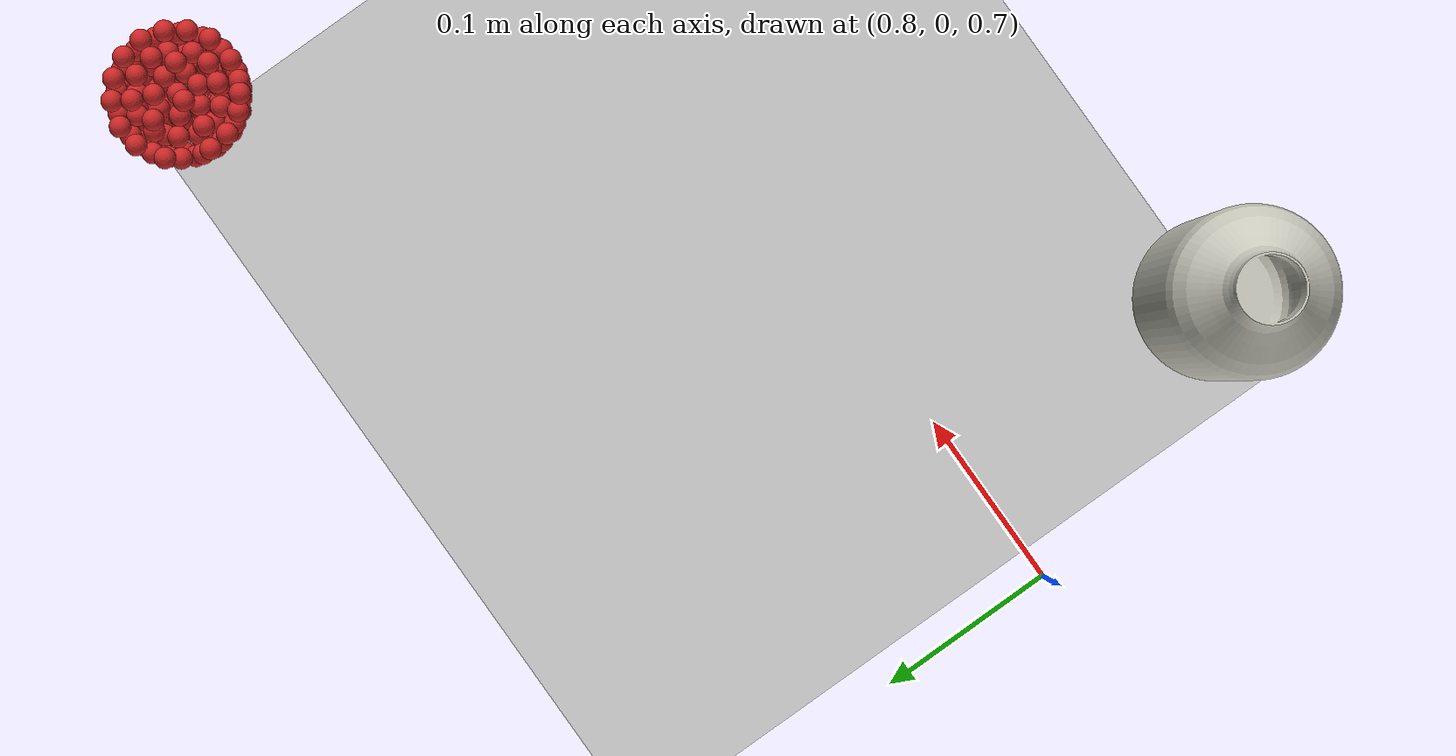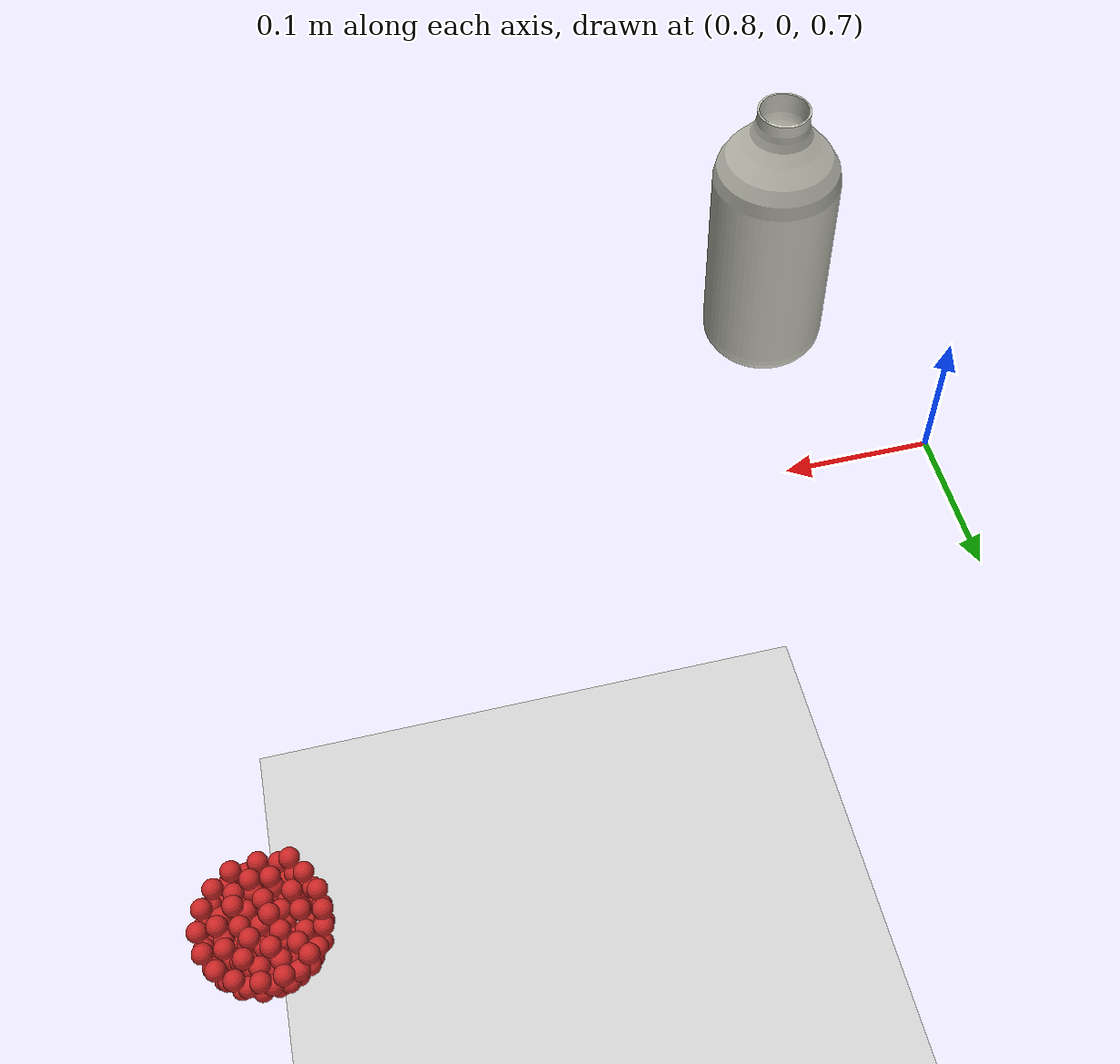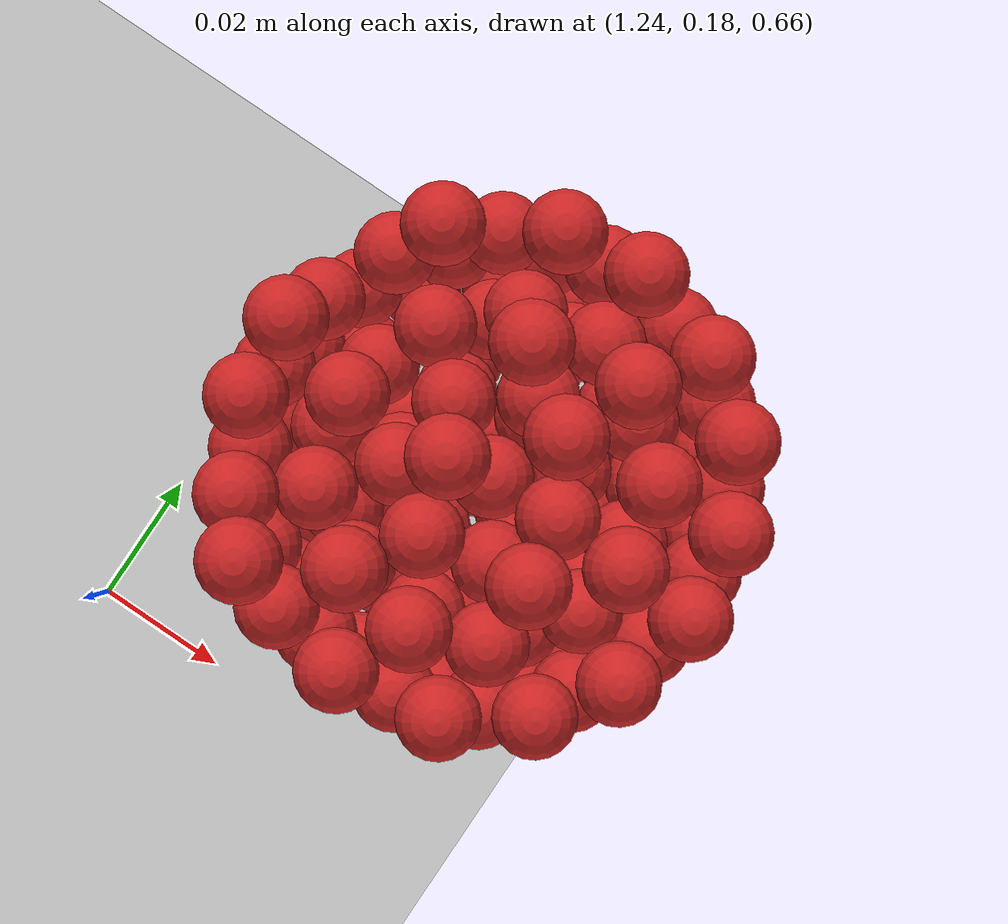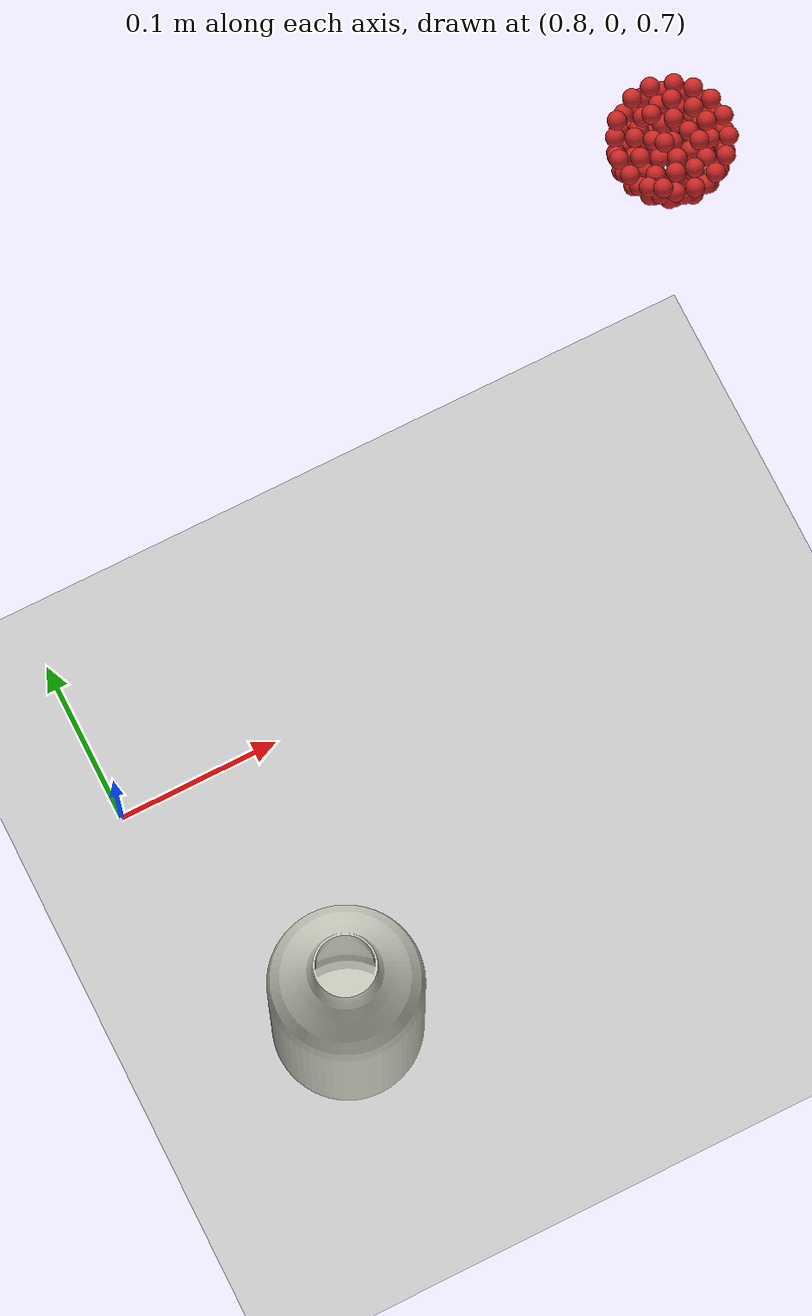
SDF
<sdf version="1.4">
 <world name="default">
  <physics type="ode">
   <gravity>0 0 -9.81</gravity>
   <ode>
    <solver><type>quick</type><iters>20</iters><sor>1</sor></solver>
    <constraints>
     <cfm>0</cfm>
     <erp>0.2</erp>
     <contact_max_correcting_vel>100</contact_max_correcting_vel>
     <contact_surface_layer>0</contact_surface_layer>
    </constraints>
   </ode>
   <real_time_update_rate>1000</real_time_update_rate>
   <max_step_size>0.001</max_step_size>
   <real_time_factor>1</real_time_factor>
  </physics>
  <light name="sun" type="directional">
   <pose>0 0 10 0 -0 0</pose>
   <diffuse>0.8 0.8 0.8 1</diffuse>
   <specular>0.2 0.2 0.2 1</specular>
   <attenuation>
    <range>1000</range>
    <constant>0.9</constant>
    <linear>0.01</linear>
    <quadratic>0.001</quadratic>
   </attenuation>
   <direction>-0.5 0.1 -0.9</direction>
  </light>
  <model name="ground_plane">
   <static>1</static>
   <link name="link">
    <collision name="collision">
     <geometry><plane><normal>0 0 1</normal><size>100 100</size></plane></geometry>
     <surface><friction><ode><mu>100</mu><mu2>50</mu2></ode></friction></surface>
    </collision>
    <visual name="visual">
     <cast_shadows>0</cast_shadows>
     <geometry><plane><normal>0 0 1</normal><size>100 100</size></plane></geometry>
     <material>
      <script><uri>file://media/materials/scripts/gazebo.material</uri><name>Gazebo/Grey</name></script>
     </material>
    </visual>
    <velocity_decay><linear>0</linear><angular>0</angular></velocity_decay>
   </link>
  </model>
  <scene><ambient>0.4 0.4 0.4 1</ambient><background>0.7 0.7 0.7 1</background><shadows>1</shadows></scene>
  <spherical_coordinates>
   <surface_model>EARTH_WGS84</surface_model>
   <latitude_deg>0</latitude_deg>
   <longitude_deg>0</longitude_deg>
   <elevation>0</elevation>
   <heading_deg>0</heading_deg>
  </spherical_coordinates>
  <model name="milk_bottle">
   <static>0</static>
   <link name="link">
    <inertial>
     <mass>0.25</mass>
     <inertia><ixx>0</ixx><ixy>0</ixy><ixz>0</ixz><iyy>0</iyy><iyz>0</iyz><izz>0</izz></inertia>
    </inertial>
    <collision name="colision1">
     <geometry><mesh><uri>model://milk_bottle/meshes/milk_bottle.dae</uri><scale>1 1 1</scale></mesh></geometry>
    </collision>
    <visual name="visual1">
     <geometry><mesh><uri>model://milk_bottle/meshes/milk_bottle.dae</uri><scale>1 1 1</scale></mesh></geometry>
     <material>
      <script><uri>file://media/materials/scripts/gazebo.material</uri><name>Gazebo/PaintedWall</name></script>
     </material>
    </visual>
    <velocity_decay><linear>0</linear><angular>0</angular></velocity_decay>
   </link>
   <pose>0.864342 -0.164381 0.752694 -0.000122 0.000148 -3e-06</pose>
  </model>
  <model name="sphere0">
   <pose>0.001008 0.018548 -0.081049 0.071962 -0.025475 0.002691</pose>
   <link name="link">
    <pose>1.27614 0.232149 0.722288 0 -0 0</pose>
    <inertial>
     <mass>0.001</mass>
     <inertia><ixx>0.004</ixx><ixy>0</ixy><ixz>0</ixz><iyy>0.004</iyy><iyz>0</iyz><izz>0.004</izz></inertia>
    </inertial>
    <collision name="collision">
     <surface>
      <contact><ode><kp>1e+10</kp><kd>1</kd></ode></contact>
      <friction><ode><mu>0.01</mu><mu2>0.01</mu2></ode></friction>
     </surface>
     <geometry><sphere><radius>0.006</radius></sphere></geometry>
    </collision>
    <visual name="visual">
     <geometry><sphere><radius>0.006</radius></sphere></geometry>
     <material>
      <script><uri>file://media/materials/scripts/gazebo.material</uri><name>Gazebo/Red</name></script>
     </material>
    </visual>
    <velocity_decay><linear>0</linear><angular>0</angular></velocity_decay>
   </link>
   <static>0</static>
  </model>
  <model name="sphere1">
   <pose>-0.016605 -0.050553 -0.032877 -0.006956 0.001233 0.006925</pose>
   <link name="link">
    <pose>1.28814 0.232149 0.722288 0 -0 0</pose>
    <inertial>
     <mass>0.001</mass>
     <inertia><ixx>0.004</ixx><ixy>0</ixy><ixz>0</ixz><iyy>0.004</iyy><iyz>0</iyz><izz>0.004</izz></inertia>
    </inertial>
    <collision name="collision">
     <surface>
      <contact><ode><kp>1e+10</kp><kd>1</kd></ode></contact>
      <friction><ode><mu>0.01</mu><mu2>0.01</mu2></ode></friction>
     </surface>
     <geometry><sphere><radius>0.006</radius></sphere></geometry>
    </collision>
    <visual name="visual">
     <geometry><sphere><radius>0.006</radius></sphere></geometry>
     <material>
      <script><uri>file://media/materials/scripts/gazebo.material</uri><name>Gazebo/Red</name></script>
     </material>
    </visual>
    <velocity_decay><linear>0</linear><angular>0</angular></velocity_decay>
   </link>
   <static>0</static>
  </model>
  <model name="sphere2">
   <pose>-0.03156 0.024433 -0.046757 0.091912 0.013346 0.004879</pose>
   <link name="link">
    <pose>1.30014 0.232149 0.722288 0 -0 0</pose>
    <inertial>
     <mass>0.001</mass>
     <inertia><ixx>0.004</ixx><ixy>0</ixy><ixz>0</ixz><iyy>0.004</iyy><iyz>0</iyz><izz>0.004</izz></inertia>
    </inertial>
    <collision name="collision">
     <surface>
      <contact><ode><kp>1e+10</kp><kd>1</kd></ode></contact>
      <friction><ode><mu>0.01</mu><mu2>0.01</mu2></ode></friction>
     </surface>
     <geometry><sphere><radius>0.006</radius></sphere></geometry>
    </collision>
    <visual name="visual">
     <geometry><sphere><radius>0.006</radius></sphere></geometry>
     <material>
      <script><uri>file://media/materials/scripts/gazebo.material</uri><name>Gazebo/Red</name></script>
     </material>
    </visual>
    <velocity_decay><linear>0</linear><angular>0</angular></velocity_decay>
   </link>
   <static>0</static>
  </model>
  <model name="sphere3">
   <pose>-0.020545 -0.054807 -0.027745 -0.009718 0.01113 0.002303</pose>
   <link name="link">
    <pose>1.27614 0.244149 0.722288 0 -0 0</pose>
    <inertial>
     <mass>0.001</mass>
     <inertia><ixx>0.004</ixx><ixy>0</ixy><ixz>0</ixz><iyy>0.004</iyy><iyz>0</iyz><izz>0.004</izz></inertia>
    </inertial>
    <collision name="collision">
     <surface>
      <contact><ode><kp>1e+10</kp><kd>1</kd></ode></contact>
      <friction><ode><mu>0.01</mu><mu2>0.01</mu2></ode></friction>
     </surface>
     <geometry><sphere><radius>0.006</radius></sphere></geometry>
    </collision>
    <visual name="visual">
     <geometry><sphere><radius>0.006</radius></sphere></geometry>
     <material>
      <script><uri>file://media/materials/scripts/gazebo.material</uri><name>Gazebo/Red</name></script>
     </material>
    </visual>
    <velocity_decay><linear>0</linear><angular>0</angular></velocity_decay>
   </link>
   <static>0</static>
  </model>
  <model name="sphere4">
   <pose>-0.019638 -0.020213 -0.048444 0.000771 -0.002935 7.9e-05</pose>
   <link name="link">
    <pose>1.28814 0.244149 0.722288 0 -0 0</pose>
    <inertial>
     <mass>0.001</mass>
     <inertia><ixx>0.004</ixx><ixy>0</ixy><ixz>0</ixz><iyy>0.004</iyy><iyz>0</iyz><izz>0.004</izz></inertia>
    </inertial>
    <collision name="collision">
     <surface>
      <contact><ode><kp>1e+10</kp><kd>1</kd></ode></contact>
      <friction><ode><mu>0.01</mu><mu2>0.01</mu2></ode></friction>
     </surface>
     <geometry><sphere><radius>0.006</radius></sphere></geometry>
    </collision>
    <visual name="visual">
     <geometry><sphere><radius>0.006</radius></sphere></geometry>
     <material>
      <script><uri>file://media/materials/scripts/gazebo.material</uri><name>Gazebo/Red</name></script>
     </material>
    </visual>
    <velocity_decay><linear>0</linear><angular>0</angular></velocity_decay>
   </link>
   <static>0</static>
  </model>
  <model name="sphere5">
   <pose>-0.011875 -0.062752 -0.06193 -0.031758 -0.011657 -0.000786</pose>
   <link name="link">
    <pose>1.30014 0.244149 0.722288 0 -0 0</pose>
    <inertial>
     <mass>0.001</mass>
     <inertia><ixx>0.004</ixx><ixy>0</ixy><ixz>0</ixz><iyy>0.004</iyy><iyz>0</iyz><izz>0.004</izz></inertia>
    </inertial>
    <collision name="collision">
     <surface>
      <contact><ode><kp>1e+10</kp><kd>1</kd></ode></contact>
      <friction><ode><mu>0.01</mu><mu2>0.01</mu2></ode></friction>
     </surface>
     <geometry><sphere><radius>0.006</radius></sphere></geometry>
    </collision>
    <visual name="visual">
     <geometry><sphere><radius>0.006</radius></sphere></geometry>
     <material>
      <script><uri>file://media/materials/scripts/gazebo.material</uri><name>Gazebo/Red</name></script>
     </material>
    </visual>
    <velocity_decay><linear>0</linear><angular>0</angular></velocity_decay>
   </link>
   <static>0</static>
  </model>
  <model name="sphere6">
   <pose>-0.0296 -0.04667 -0.030311 0.00043 0.003534 0.00235</pose>
   <link name="link">
    <pose>1.27614 0.256149 0.722288 0 -0 0</pose>
    <inertial>
     <mass>0.001</mass>
     <inertia><ixx>0.004</ixx><ixy>0</ixy><ixz>0</ixz><iyy>0.004</iyy><iyz>0</iyz><izz>0.004</izz></inertia>
    </inertial>
    <collision name="collision">
     <surface>
      <contact><ode><kp>1e+10</kp><kd>1</kd></ode></contact>
      <friction><ode><mu>0.01</mu><mu2>0.01</mu2></ode></friction>
     </surface>
     <geometry><sphere><radius>0.006</radius></sphere></geometry>
    </collision>
    <visual name="visual">
     <geometry><sphere><radius>0.006</radius></sphere></geometry>
     <material>
      <script><uri>file://media/materials/scripts/gazebo.material</uri><name>Gazebo/Red</name></script>
     </material>
    </visual>
    <velocity_decay><linear>0</linear><angular>0</angular></velocity_decay>
   </link>
   <static>0</static>
  </model>
  <model name="sphere7">
   <pose>-0.046009 -0.034845 -0.037973 0.003183 0.007088 -0.001687</pose>
   <link name="link">
    <pose>1.28814 0.256149 0.722288 0 -0 0</pose>
    <inertial>
     <mass>0.001</mass>
     <inertia><ixx>0.004</ixx><ixy>0</ixy><ixz>0</ixz><iyy>0.004</iyy><iyz>0</iyz><izz>0.004</izz></inertia>
    </inertial>
    <collision name="collision">
     <surface>
      <contact><ode><kp>1e+10</kp><kd>1</kd></ode></contact>
      <friction><ode><mu>0.01</mu><mu2>0.01</mu2></ode></friction>
     </surface>
     <geometry><sphere><radius>0.006</radius></sphere></geometry>
    </collision>
    <visual name="visual">
     <geometry><sphere><radius>0.006</radius></sphere></geometry>
     <material>
      <script><uri>file://media/materials/scripts/gazebo.material</uri><name>Gazebo/Red</name></script>
     </material>
    </visual>
    <velocity_decay><linear>0</linear><angular>0</angular></velocity_decay>
   </link>
   <static>0</static>
  </model>
  <model name="sphere8">
   <pose>-0.009657 -0.049791 -0.053172 0.004137 0.002085 4.5e-05</pose>
   <link name="link">
    <pose>1.30014 0.256149 0.722288 0 -0 0</pose>
    <inertial>
     <mass>0.001</mass>
     <inertia><ixx>0.004</ixx><ixy>0</ixy><ixz>0</ixz><iyy>0.004</iyy><iyz>0</iyz><izz>0.004</izz></inertia>
    </inertial>
    <collision name="collision">
     <surface>
      <contact><ode><kp>1e+10</kp><kd>1</kd></ode></contact>
      <friction><ode><mu>0.01</mu><mu2>0.01</mu2></ode></friction>
     </surface>
     <geometry><sphere><radius>0.006</radius></sphere></geometry>
    </collision>
    <visual name="visual">
     <geometry><sphere><radius>0.006</radius></sphere></geometry>
     <material>
      <script><uri>file://media/materials/scripts/gazebo.material</uri><name>Gazebo/Red</name></script>
     </material>
    </visual>
    <velocity_decay><linear>0</linear><angular>0</angular></velocity_decay>
   </link>
   <static>0</static>
  </model>
  <model name="sphere9">
   <pose>0.002803 -0.004202 -0.059302 0.001486 -0.001493 8.3e-05</pose>
   <link name="link">
    <pose>1.27614 0.232149 0.734288 0 -0 0</pose>
    <inertial>
     <mass>0.001</mass>
     <inertia><ixx>0.004</ixx><ixy>0</ixy><ixz>0</ixz><iyy>0.004</iyy><iyz>0</iyz><izz>0.004</izz></inertia>
    </inertial>
    <collision name="collision">
     <surface>
      <contact><ode><kp>1e+10</kp><kd>1</kd></ode></contact>
      <friction><ode><mu>0.01</mu><mu2>0.01</mu2></ode></friction>
     </surface>
     <geometry><sphere><radius>0.006</radius></sphere></geometry>
    </collision>
    <visual name="visual">
     <geometry><sphere><radius>0.006</radius></sphere></geometry>
     <material>
      <script><uri>file://media/materials/scripts/gazebo.material</uri><name>Gazebo/Red</name></script>
     </material>
    </visual>
    <velocity_decay><linear>0</linear><angular>0</angular></velocity_decay>
   </link>
   <static>0</static>
  </model>
  <model name="sphere10">
   <pose>-0.037418 -0.015098 -0.056492 0.011145 0.009968 -0.000589</pose>
   <link name="link">
    <pose>1.28814 0.232149 0.734288 0 -0 0</pose>
    <inertial>
     <mass>0.001</mass>
     <inertia><ixx>0.004</ixx><ixy>0</ixy><ixz>0</ixz><iyy>0.004</iyy><iyz>0</iyz><izz>0.004</izz></inertia>
    </inertial>
    <collision name="collision">
     <surface>
      <contact><ode><kp>1e+10</kp><kd>1</kd></ode></contact>
      <friction><ode><mu>0.01</mu><mu2>0.01</mu2></ode></friction>
     </surface>
     <geometry><sphere><radius>0.006</radius></sphere></geometry>
    </collision>
    <visual name="visual">
     <geometry><sphere><radius>0.006</radius></sphere></geometry>
     <material>
      <script><uri>file://media/materials/scripts/gazebo.material</uri><name>Gazebo/Red</name></script>
     </material>
    </visual>
    <velocity_decay><linear>0</linear><angular>0</angular></velocity_decay>
   </link>
   <static>0</static>
  </model>
  <model name="sphere11">
   <pose>-0.029988 -0.048635 -0.064378 -0.02484 -0.002739 -4e-05</pose>
   <link name="link">
    <pose>1.30014 0.232149 0.734288 0 -0 0</pose>
    <inertial>
     <mass>0.001</mass>
     <inertia><ixx>0.004</ixx><ixy>0</ixy><ixz>0</ixz><iyy>0.004</iyy><iyz>0</iyz><izz>0.004</izz></inertia>
    </inertial>
    <collision name="collision">
     <surface>
      <contact><ode><kp>1e+10</kp><kd>1</kd></ode></contact>
      <friction><ode><mu>0.01</mu><mu2>0.01</mu2></ode></friction>
     </surface>
     <geometry><sphere><radius>0.006</radius></sphere></geometry>
    </collision>
    <visual name="visual">
     <geometry><sphere><radius>0.006</radius></sphere></geometry>
     <material>
      <script><uri>file://media/materials/scripts/gazebo.material</uri><name>Gazebo/Red</name></script>
     </material>
    </visual>
    <velocity_decay><linear>0</linear><angular>0</angular></velocity_decay>
   </link>
   <static>0</static>
  </model>
  <model name="sphere12">
   <pose>-0.013302 -0.013665 -0.065337 0.000626 0.0014 -0.000924</pose>
   <link name="link">
    <pose>1.27614 0.244149 0.734288 0 -0 0</pose>
    <inertial>
     <mass>0.001</mass>
     <inertia><ixx>0.004</ixx><ixy>0</ixy><ixz>0</ixz><iyy>0.004</iyy><iyz>0</iyz><izz>0.004</izz></inertia>
    </inertial>
    <collision name="collision">
     <surface>
      <contact><ode><kp>1e+10</kp><kd>1</kd></ode></contact>
      <friction><ode><mu>0.01</mu><mu2>0.01</mu2></ode></friction>
     </surface>
     <geometry><sphere><radius>0.006</radius></sphere></geometry>
    </collision>
    <visual name="visual">
     <geometry><sphere><radius>0.006</radius></sphere></geometry>
     <material>
      <script><uri>file://media/materials/scripts/gazebo.material</uri><name>Gazebo/Red</name></script>
     </material>
    </visual>
    <velocity_decay><linear>0</linear><angular>0</angular></velocity_decay>
   </link>
   <static>0</static>
  </model>
  <model name="sphere13">
   <pose>0.00022 -0.017936 -0.07352 6e-05 -0.005185 -0.000187</pose>
   <link name="link">
    <pose>1.28814 0.244149 0.734288 0 -0 0</pose>
    <inertial>
     <mass>0.001</mass>
     <inertia><ixx>0.004</ixx><ixy>0</ixy><ixz>0</ixz><iyy>0.004</iyy><iyz>0</iyz><izz>0.004</izz></inertia>
    </inertial>
    <collision name="collision">
     <surface>
      <contact><ode><kp>1e+10</kp><kd>1</kd></ode></contact>
      <friction><ode><mu>0.01</mu><mu2>0.01</mu2></ode></friction>
     </surface>
     <geometry><sphere><radius>0.006</radius></sphere></geometry>
    </collision>
    <visual name="visual">
     <geometry><sphere><radius>0.006</radius></sphere></geometry>
     <material>
      <script><uri>file://media/materials/scripts/gazebo.material</uri><name>Gazebo/Red</name></script>
     </material>
    </visual>
    <velocity_decay><linear>0</linear><angular>0</angular></velocity_decay>
   </link>
   <static>0</static>
  </model>
  <model name="sphere14">
   <pose>-0.004564 -0.045405 -0.07152 -0.022207 -0.007884 9.3e-05</pose>
   <link name="link">
    <pose>1.30014 0.244149 0.734288 0 -0 0</pose>
    <inertial>
     <mass>0.001</mass>
     <inertia><ixx>0.004</ixx><ixy>0</ixy><ixz>0</ixz><iyy>0.004</iyy><iyz>0</iyz><izz>0.004</izz></inertia>
    </inertial>
    <collision name="collision">
     <surface>
      <contact><ode><kp>1e+10</kp><kd>1</kd></ode></contact>
      <friction><ode><mu>0.01</mu><mu2>0.01</mu2></ode></friction>
     </surface>
     <geometry><sphere><radius>0.006</radius></sphere></geometry>
    </collision>
    <visual name="visual">
     <geometry><sphere><radius>0.006</radius></sphere></geometry>
     <material>
      <script><uri>file://media/materials/scripts/gazebo.material</uri><name>Gazebo/Red</name></script>
     </material>
    </visual>
    <velocity_decay><linear>0</linear><angular>0</angular></velocity_decay>
   </link>
   <static>0</static>
  </model>
  <model name="sphere15">
   <pose>-0.022106 -0.038657 -0.06072 0.004887 -0.002802 -0.005754</pose>
   <link name="link">
    <pose>1.27614 0.256149 0.734288 0 -0 0</pose>
    <inertial>
     <mass>0.001</mass>
     <inertia><ixx>0.004</ixx><ixy>0</ixy><ixz>0</ixz><iyy>0.004</iyy><iyz>0</iyz><izz>0.004</izz></inertia>
    </inertial>
    <collision name="collision">
     <surface>
      <contact><ode><kp>1e+10</kp><kd>1</kd></ode></contact>
      <friction><ode><mu>0.01</mu><mu2>0.01</mu2></ode></friction>
     </surface>
     <geometry><sphere><radius>0.006</radius></sphere></geometry>
    </collision>
    <visual name="visual">
     <geometry><sphere><radius>0.006</radius></sphere></geometry>
     <material>
      <script><uri>file://media/materials/scripts/gazebo.material</uri><name>Gazebo/Red</name></script>
     </material>
    </visual>
    <velocity_decay><linear>0</linear><angular>0</angular></velocity_decay>
   </link>
   <static>0</static>
  </model>
  <model name="sphere16">
   <pose>-0.042632 -0.028102 -0.05267 0.008144 0.01256 -0.000636</pose>
   <link name="link">
    <pose>1.28814 0.256149 0.734288 0 -0 0</pose>
    <inertial>
     <mass>0.001</mass>
     <inertia><ixx>0.004</ixx><ixy>0</ixy><ixz>0</ixz><iyy>0.004</iyy><iyz>0</iyz><izz>0.004</izz></inertia>
    </inertial>
    <collision name="collision">
     <surface>
      <contact><ode><kp>1e+10</kp><kd>1</kd></ode></contact>
      <friction><ode><mu>0.01</mu><mu2>0.01</mu2></ode></friction>
     </surface>
     <geometry><sphere><radius>0.006</radius></sphere></geometry>
    </collision>
    <visual name="visual">
     <geometry><sphere><radius>0.006</radius></sphere></geometry>
     <material>
      <script><uri>file://media/materials/scripts/gazebo.material</uri><name>Gazebo/Red</name></script>
     </material>
    </visual>
    <velocity_decay><linear>0</linear><angular>0</angular></velocity_decay>
   </link>
   <static>0</static>
  </model>
  <model name="sphere17">
   <pose>-0.052029 0.012497 -0.043813 0.022962 0.021947 0.001176</pose>
   <link name="link">
    <pose>1.30014 0.256149 0.734288 0 -0 0</pose>
    <inertial>
     <mass>0.001</mass>
     <inertia><ixx>0.004</ixx><ixy>0</ixy><ixz>0</ixz><iyy>0.004</iyy><iyz>0</iyz><izz>0.004</izz></inertia>
    </inertial>
    <collision name="collision">
     <surface>
      <contact><ode><kp>1e+10</kp><kd>1</kd></ode></contact>
      <friction><ode><mu>0.01</mu><mu2>0.01</mu2></ode></friction>
     </surface>
     <geometry><sphere><radius>0.006</radius></sphere></geometry>
    </collision>
    <visual name="visual">
     <geometry><sphere><radius>0.006</radius></sphere></geometry>
     <material>
      <script><uri>file://media/materials/scripts/gazebo.material</uri><name>Gazebo/Red</name></script>
     </material>
    </visual>
    <velocity_decay><linear>0</linear><angular>0</angular></velocity_decay>
   </link>
   <static>0</static>
  </model>
  <model name="sphere18">
   <pose>-0.000387 -0.016964 -0.094649 -0.001726 -0.012766 0.000419</pose>
   <link name="link">
    <pose>1.27614 0.232149 0.746288 0 -0 0</pose>
    <inertial>
     <mass>0.001</mass>
     <inertia><ixx>0.004</ixx><ixy>0</ixy><ixz>0</ixz><iyy>0.004</iyy><iyz>0</iyz><izz>0.004</izz></inertia>
    </inertial>
    <collision name="collision">
     <surface>
      <contact><ode><kp>1e+10</kp><kd>1</kd></ode></contact>
      <friction><ode><mu>0.01</mu><mu2>0.01</mu2></ode></friction>
     </surface>
     <geometry><sphere><radius>0.006</radius></sphere></geometry>
    </collision>
    <visual name="visual">
     <geometry><sphere><radius>0.006</radius></sphere></geometry>
     <material>
      <script><uri>file://media/materials/scripts/gazebo.material</uri><name>Gazebo/Red</name></script>
     </material>
    </visual>
    <velocity_decay><linear>0</linear><angular>0</angular></velocity_decay>
   </link>
   <static>0</static>
  </model>
  <model name="sphere19">
   <pose>-0.011825 -0.03433 -0.050777 0.003505 -0.000296 -0.001107</pose>
   <link name="link">
    <pose>1.28814 0.232149 0.746288 0 -0 0</pose>
    <inertial>
     <mass>0.001</mass>
     <inertia><ixx>0.004</ixx><ixy>0</ixy><ixz>0</ixz><iyy>0.004</iyy><iyz>0</iyz><izz>0.004</izz></inertia>
    </inertial>
    <collision name="collision">
     <surface>
      <contact><ode><kp>1e+10</kp><kd>1</kd></ode></contact>
      <friction><ode><mu>0.01</mu><mu2>0.01</mu2></ode></friction>
     </surface>
     <geometry><sphere><radius>0.006</radius></sphere></geometry>
    </collision>
    <visual name="visual">
     <geometry><sphere><radius>0.006</radius></sphere></geometry>
     <material>
      <script><uri>file://media/materials/scripts/gazebo.material</uri><name>Gazebo/Red</name></script>
     </material>
    </visual>
    <velocity_decay><linear>0</linear><angular>0</angular></velocity_decay>
   </link>
   <static>0</static>
  </model>
  <model name="sphere20">
   <pose>-0.011569 -0.049023 -0.061031 -0.015507 -0.005207 0.000311</pose>
   <link name="link">
    <pose>1.30014 0.232149 0.746288 0 -0 0</pose>
    <inertial>
     <mass>0.001</mass>
     <inertia><ixx>0.004</ixx><ixy>0</ixy><ixz>0</ixz><iyy>0.004</iyy><iyz>0</iyz><izz>0.004</izz></inertia>
    </inertial>
    <collision name="collision">
     <surface>
      <contact><ode><kp>1e+10</kp><kd>1</kd></ode></contact>
      <friction><ode><mu>0.01</mu><mu2>0.01</mu2></ode></friction>
     </surface>
     <geometry><sphere><radius>0.006</radius></sphere></geometry>
    </collision>
    <visual name="visual">
     <geometry><sphere><radius>0.006</radius></sphere></geometry>
     <material>
      <script><uri>file://media/materials/scripts/gazebo.material</uri><name>Gazebo/Red</name></script>
     </material>
    </visual>
    <velocity_decay><linear>0</linear><angular>0</angular></velocity_decay>
   </link>
   <static>0</static>
  </model>
  <model name="sphere21">
   <pose>-0.018044 -0.048968 -0.040357 -0.006757 -0.00101 -0.000459</pose>
   <link name="link">
    <pose>1.27614 0.244149 0.746288 0 -0 0</pose>
    <inertial>
     <mass>0.001</mass>
     <inertia><ixx>0.004</ixx><ixy>0</ixy><ixz>0</ixz><iyy>0.004</iyy><iyz>0</iyz><izz>0.004</izz></inertia>
    </inertial>
    <collision name="collision">
     <surface>
      <contact><ode><kp>1e+10</kp><kd>1</kd></ode></contact>
      <friction><ode><mu>0.01</mu><mu2>0.01</mu2></ode></friction>
     </surface>
     <geometry><sphere><radius>0.006</radius></sphere></geometry>
    </collision>
    <visual name="visual">
     <geometry><sphere><radius>0.006</radius></sphere></geometry>
     <material>
      <script><uri>file://media/materials/scripts/gazebo.material</uri><name>Gazebo/Red</name></script>
     </material>
    </visual>
    <velocity_decay><linear>0</linear><angular>0</angular></velocity_decay>
   </link>
   <static>0</static>
  </model>
  <model name="sphere22">
   <pose>-0.024387 -0.02344 -0.068523 0.010353 -0.000228 -0.00049</pose>
   <link name="link">
    <pose>1.28814 0.244149 0.746288 0 -0 0</pose>
    <inertial>
     <mass>0.001</mass>
     <inertia><ixx>0.004</ixx><ixy>0</ixy><ixz>0</ixz><iyy>0.004</iyy><iyz>0</iyz><izz>0.004</izz></inertia>
    </inertial>
    <collision name="collision">
     <surface>
      <contact><ode><kp>1e+10</kp><kd>1</kd></ode></contact>
      <friction><ode><mu>0.01</mu><mu2>0.01</mu2></ode></friction>
     </surface>
     <geometry><sphere><radius>0.006</radius></sphere></geometry>
    </collision>
    <visual name="visual">
     <geometry><sphere><radius>0.006</radius></sphere></geometry>
     <material>
      <script><uri>file://media/materials/scripts/gazebo.material</uri><name>Gazebo/Red</name></script>
     </material>
    </visual>
    <velocity_decay><linear>0</linear><angular>0</angular></velocity_decay>
   </link>
   <static>0</static>
  </model>
  <model name="sphere23">
   <pose>-0.021361 -0.02482 -0.081837 0.004586 -0.001445 -0.000687</pose>
   <link name="link">
    <pose>1.30014 0.244149 0.746288 0 -0 0</pose>
    <inertial>
     <mass>0.001</mass>
     <inertia><ixx>0.004</ixx><ixy>0</ixy><ixz>0</ixz><iyy>0.004</iyy><iyz>0</iyz><izz>0.004</izz></inertia>
    </inertial>
    <collision name="collision">
     <surface>
      <contact><ode><kp>1e+10</kp><kd>1</kd></ode></contact>
      <friction><ode><mu>0.01</mu><mu2>0.01</mu2></ode></friction>
     </surface>
     <geometry><sphere><radius>0.006</radius></sphere></geometry>
    </collision>
    <visual name="visual">
     <geometry><sphere><radius>0.006</radius></sphere></geometry>
     <material>
      <script><uri>file://media/materials/scripts/gazebo.material</uri><name>Gazebo/Red</name></script>
     </material>
    </visual>
    <velocity_decay><linear>0</linear><angular>0</angular></velocity_decay>
   </link>
   <static>0</static>
  </model>
  <model name="sphere24">
   <pose>-0.032333 -0.03788 -0.046941 0.000676 0.001702 0.000337</pose>
   <link name="link">
    <pose>1.27614 0.256149 0.746288 0 -0 0</pose>
    <inertial>
     <mass>0.001</mass>
     <inertia><ixx>0.004</ixx><ixy>0</ixy><ixz>0</ixz><iyy>0.004</iyy><iyz>0</iyz><izz>0.004</izz></inertia>
    </inertial>
    <collision name="collision">
     <surface>
      <contact><ode><kp>1e+10</kp><kd>1</kd></ode></contact>
      <friction><ode><mu>0.01</mu><mu2>0.01</mu2></ode></friction>
     </surface>
     <geometry><sphere><radius>0.006</radius></sphere></geometry>
    </collision>
    <visual name="visual">
     <geometry><sphere><radius>0.006</radius></sphere></geometry>
     <material>
      <script><uri>file://media/materials/scripts/gazebo.material</uri><name>Gazebo/Red</name></script>
     </material>
    </visual>
    <velocity_decay><linear>0</linear><angular>0</angular></velocity_decay>
   </link>
   <static>0</static>
  </model>
  <model name="sphere25">
   <pose>-0.046109 -0.02712 -0.046509 -0.001532 0.002019 -6e-05</pose>
   <link name="link">
    <pose>1.28814 0.256149 0.746288 0 -0 0</pose>
    <inertial>
     <mass>0.001</mass>
     <inertia><ixx>0.004</ixx><ixy>0</ixy><ixz>0</ixz><iyy>0.004</iyy><iyz>0</iyz><izz>0.004</izz></inertia>
    </inertial>
    <collision name="collision">
     <surface>
      <contact><ode><kp>1e+10</kp><kd>1</kd></ode></contact>
      <friction><ode><mu>0.01</mu><mu2>0.01</mu2></ode></friction>
     </surface>
     <geometry><sphere><radius>0.006</radius></sphere></geometry>
    </collision>
    <visual name="visual">
     <geometry><sphere><radius>0.006</radius></sphere></geometry>
     <material>
      <script><uri>file://media/materials/scripts/gazebo.material</uri><name>Gazebo/Red</name></script>
     </material>
    </visual>
    <velocity_decay><linear>0</linear><angular>0</angular></velocity_decay>
   </link>
   <static>0</static>
  </model>
  <model name="sphere26">
   <pose>-0.009544 -0.028372 -0.052766 -0.002954 -0.001273 -0.00138</pose>
   <link name="link">
    <pose>1.30014 0.256149 0.746288 0 -0 0</pose>
    <inertial>
     <mass>0.001</mass>
     <inertia><ixx>0.004</ixx><ixy>0</ixy><ixz>0</ixz><iyy>0.004</iyy><iyz>0</iyz><izz>0.004</izz></inertia>
    </inertial>
    <collision name="collision">
     <surface>
      <contact><ode><kp>1e+10</kp><kd>1</kd></ode></contact>
      <friction><ode><mu>0.01</mu><mu2>0.01</mu2></ode></friction>
     </surface>
     <geometry><sphere><radius>0.006</radius></sphere></geometry>
    </collision>
    <visual name="visual">
     <geometry><sphere><radius>0.006</radius></sphere></geometry>
     <material>
      <script><uri>file://media/materials/scripts/gazebo.material</uri><name>Gazebo/Red</name></script>
     </material>
    </visual>
    <velocity_decay><linear>0</linear><angular>0</angular></velocity_decay>
   </link>
   <static>0</static>
  </model>
  <model name="sphere27">
   <pose>-0.011428 -0.041118 -0.060171 -0.002115 0.000878 0.00303</pose>
   <link name="link">
    <pose>1.27614 0.232149 0.758288 0 -0 0</pose>
    <inertial>
     <mass>0.001</mass>
     <inertia><ixx>0.004</ixx><ixy>0</ixy><ixz>0</ixz><iyy>0.004</iyy><iyz>0</iyz><izz>0.004</izz></inertia>
    </inertial>
    <collision name="collision">
     <surface>
      <contact><ode><kp>1e+10</kp><kd>1</kd></ode></contact>
      <friction><ode><mu>0.01</mu><mu2>0.01</mu2></ode></friction>
     </surface>
     <geometry><sphere><radius>0.006</radius></sphere></geometry>
    </collision>
    <visual name="visual">
     <geometry><sphere><radius>0.006</radius></sphere></geometry>
     <material>
      <script><uri>file://media/materials/scripts/gazebo.material</uri><name>Gazebo/Red</name></script>
     </material>
    </visual>
    <velocity_decay><linear>0</linear><angular>0</angular></velocity_decay>
   </link>
   <static>0</static>
  </model>
  <model name="sphere28">
   <pose>0.004063 -0.037692 -0.060857 -0.002287 -0.000801 8.6e-05</pose>
   <link name="link">
    <pose>1.28814 0.232149 0.758288 0 -0 0</pose>
    <inertial>
     <mass>0.001</mass>
     <inertia><ixx>0.004</ixx><ixy>0</ixy><ixz>0</ixz><iyy>0.004</iyy><iyz>0</iyz><izz>0.004</izz></inertia>
    </inertial>
    <collision name="collision">
     <surface>
      <contact><ode><kp>1e+10</kp><kd>1</kd></ode></contact>
      <friction><ode><mu>0.01</mu><mu2>0.01</mu2></ode></friction>
     </surface>
     <geometry><sphere><radius>0.006</radius></sphere></geometry>
    </collision>
    <visual name="visual">
     <geometry><sphere><radius>0.006</radius></sphere></geometry>
     <material>
      <script><uri>file://media/materials/scripts/gazebo.material</uri><name>Gazebo/Red</name></script>
     </material>
    </visual>
    <velocity_decay><linear>0</linear><angular>0</angular></velocity_decay>
   </link>
   <static>0</static>
  </model>
  <model name="sphere29">
   <pose>-0.015729 -0.059733 -0.063985 -0.022001 0.008778 0.006506</pose>
   <link name="link">
    <pose>1.30014 0.232149 0.758288 0 -0 0</pose>
    <inertial>
     <mass>0.001</mass>
     <inertia><ixx>0.004</ixx><ixy>0</ixy><ixz>0</ixz><iyy>0.004</iyy><iyz>0</iyz><izz>0.004</izz></inertia>
    </inertial>
    <collision name="collision">
     <surface>
      <contact><ode><kp>1e+10</kp><kd>1</kd></ode></contact>
      <friction><ode><mu>0.01</mu><mu2>0.01</mu2></ode></friction>
     </surface>
     <geometry><sphere><radius>0.006</radius></sphere></geometry>
    </collision>
    <visual name="visual">
     <geometry><sphere><radius>0.006</radius></sphere></geometry>
     <material>
      <script><uri>file://media/materials/scripts/gazebo.material</uri><name>Gazebo/Red</name></script>
     </material>
    </visual>
    <velocity_decay><linear>0</linear><angular>0</angular></velocity_decay>
   </link>
   <static>0</static>
  </model>
  <model name="sphere30">
   <pose>-0.016608 -0.019493 -0.069255 0.000168 -0.004008 0.001293</pose>
   <link name="link">
    <pose>1.27614 0.244149 0.758288 0 -0 0</pose>
    <inertial>
     <mass>0.001</mass>
     <inertia><ixx>0.004</ixx><ixy>0</ixy><ixz>0</ixz><iyy>0.004</iyy><iyz>0</iyz><izz>0.004</izz></inertia>
    </inertial>
    <collision name="collision">
     <surface>
      <contact><ode><kp>1e+10</kp><kd>1</kd></ode></contact>
      <friction><ode><mu>0.01</mu><mu2>0.01</mu2></ode></friction>
     </surface>
     <geometry><sphere><radius>0.006</radius></sphere></geometry>
    </collision>
    <visual name="visual">
     <geometry><sphere><radius>0.006</radius></sphere></geometry>
     <material>
      <script><uri>file://media/materials/scripts/gazebo.material</uri><name>Gazebo/Red</name></script>
     </material>
    </visual>
    <velocity_decay><linear>0</linear><angular>0</angular></velocity_decay>
   </link>
   <static>0</static>
  </model>
  <model name="sphere31">
   <pose>-0.031581 -0.022716 -0.075835 -0.000493 -0.000743 -0.000499</pose>
   <link name="link">
    <pose>1.28814 0.244149 0.758288 0 -0 0</pose>
    <inertial>
     <mass>0.001</mass>
     <inertia><ixx>0.004</ixx><ixy>0</ixy><ixz>0</ixz><iyy>0.004</iyy><iyz>0</iyz><izz>0.004</izz></inertia>
    </inertial>
    <collision name="collision">
     <surface>
      <contact><ode><kp>1e+10</kp><kd>1</kd></ode></contact>
      <friction><ode><mu>0.01</mu><mu2>0.01</mu2></ode></friction>
     </surface>
     <geometry><sphere><radius>0.006</radius></sphere></geometry>
    </collision>
    <visual name="visual">
     <geometry><sphere><radius>0.006</radius></sphere></geometry>
     <material>
      <script><uri>file://media/materials/scripts/gazebo.material</uri><name>Gazebo/Red</name></script>
     </material>
    </visual>
    <velocity_decay><linear>0</linear><angular>0</angular></velocity_decay>
   </link>
   <static>0</static>
  </model>
  <model name="sphere32">
   <pose>-0.014536 -0.033952 -0.059234 0.001465 0.017426 -0.004103</pose>
   <link name="link">
    <pose>1.30014 0.244149 0.758288 0 -0 0</pose>
    <inertial>
     <mass>0.001</mass>
     <inertia><ixx>0.004</ixx><ixy>0</ixy><ixz>0</ixz><iyy>0.004</iyy><iyz>0</iyz><izz>0.004</izz></inertia>
    </inertial>
    <collision name="collision">
     <surface>
      <contact><ode><kp>1e+10</kp><kd>1</kd></ode></contact>
      <friction><ode><mu>0.01</mu><mu2>0.01</mu2></ode></friction>
     </surface>
     <geometry><sphere><radius>0.006</radius></sphere></geometry>
    </collision>
    <visual name="visual">
     <geometry><sphere><radius>0.006</radius></sphere></geometry>
     <material>
      <script><uri>file://media/materials/scripts/gazebo.material</uri><name>Gazebo/Red</name></script>
     </material>
    </visual>
    <velocity_decay><linear>0</linear><angular>0</angular></velocity_decay>
   </link>
   <static>0</static>
  </model>
  <model name="sphere33">
   <pose>0.022358 -0.024231 -0.158207 0.008135 -0.067468 -0.001806</pose>
   <link name="link">
    <pose>1.27614 0.256149 0.758288 0 -0 0</pose>
    <inertial>
     <mass>0.001</mass>
     <inertia><ixx>0.004</ixx><ixy>0</ixy><ixz>0</ixz><iyy>0.004</iyy><iyz>0</iyz><izz>0.004</izz></inertia>
    </inertial>
    <collision name="collision">
     <surface>
      <contact><ode><kp>1e+10</kp><kd>1</kd></ode></contact>
      <friction><ode><mu>0.01</mu><mu2>0.01</mu2></ode></friction>
     </surface>
     <geometry><sphere><radius>0.006</radius></sphere></geometry>
    </collision>
    <visual name="visual">
     <geometry><sphere><radius>0.006</radius></sphere></geometry>
     <material>
      <script><uri>file://media/materials/scripts/gazebo.material</uri><name>Gazebo/Red</name></script>
     </material>
    </visual>
    <velocity_decay><linear>0</linear><angular>0</angular></velocity_decay>
   </link>
   <static>0</static>
  </model>
  <model name="sphere34">
   <pose>-0.035717 -0.017693 -0.09733 0.01088 -0.00927 -0.001261</pose>
   <link name="link">
    <pose>1.28814 0.256149 0.758288 0 -0 0</pose>
    <inertial>
     <mass>0.001</mass>
     <inertia><ixx>0.004</ixx><ixy>0</ixy><ixz>0</ixz><iyy>0.004</iyy><iyz>0</iyz><izz>0.004</izz></inertia>
    </inertial>
    <collision name="collision">
     <surface>
      <contact><ode><kp>1e+10</kp><kd>1</kd></ode></contact>
      <friction><ode><mu>0.01</mu><mu2>0.01</mu2></ode></friction>
     </surface>
     <geometry><sphere><radius>0.006</radius></sphere></geometry>
    </collision>
    <visual name="visual">
     <geometry><sphere><radius>0.006</radius></sphere></geometry>
     <material>
      <script><uri>file://media/materials/scripts/gazebo.material</uri><name>Gazebo/Red</name></script>
     </material>
    </visual>
    <velocity_decay><linear>0</linear><angular>0</angular></velocity_decay>
   </link>
   <static>0</static>
  </model>
  <model name="sphere35">
   <pose>-0.014164 -0.038417 -0.076132 -0.003633 0.002493 -3.7e-05</pose>
   <link name="link">
    <pose>1.30014 0.256149 0.758288 0 -0 0</pose>
    <inertial>
     <mass>0.001</mass>
     <inertia><ixx>0.004</ixx><ixy>0</ixy><ixz>0</ixz><iyy>0.004</iyy><iyz>0</iyz><izz>0.004</izz></inertia>
    </inertial>
    <collision name="collision">
     <surface>
      <contact><ode><kp>1e+10</kp><kd>1</kd></ode></contact>
      <friction><ode><mu>0.01</mu><mu2>0.01</mu2></ode></friction>
     </surface>
     <geometry><sphere><radius>0.006</radius></sphere></geometry>
    </collision>
    <visual name="visual">
     <geometry><sphere><radius>0.006</radius></sphere></geometry>
     <material>
      <script><uri>file://media/materials/scripts/gazebo.material</uri><name>Gazebo/Red</name></script>
     </material>
    </visual>
    <velocity_decay><linear>0</linear><angular>0</angular></velocity_decay>
   </link>
   <static>0</static>
  </model>
  <model name="sphere36">
   <pose>-0.006579 -0.023408 -0.080876 0.002769 0.00054 0.000353</pose>
   <link name="link">
    <pose>1.27614 0.232149 0.770288 0 -0 0</pose>
    <inertial>
     <mass>0.001</mass>
     <inertia><ixx>0.004</ixx><ixy>0</ixy><ixz>0</ixz><iyy>0.004</iyy><iyz>0</iyz><izz>0.004</izz></inertia>
    </inertial>
    <collision name="collision">
     <surface>
      <contact><ode><kp>1e+10</kp><kd>1</kd></ode></contact>
      <friction><ode><mu>0.01</mu><mu2>0.01</mu2></ode></friction>
     </surface>
     <geometry><sphere><radius>0.006</radius></sphere></geometry>
    </collision>
    <visual name="visual">
     <geometry><sphere><radius>0.006</radius></sphere></geometry>
     <material>
      <script><uri>file://media/materials/scripts/gazebo.material</uri><name>Gazebo/Red</name></script>
     </material>
    </visual>
    <velocity_decay><linear>0</linear><angular>0</angular></velocity_decay>
   </link>
   <static>0</static>
  </model>
  <model name="sphere37">
   <pose>-0.012535 -0.022359 -0.097847 0.003619 -0.002644 1.4e-05</pose>
   <link name="link">
    <pose>1.28814 0.232149 0.770288 0 -0 0</pose>
    <inertial>
     <mass>0.001</mass>
     <inertia><ixx>0.004</ixx><ixy>0</ixy><ixz>0</ixz><iyy>0.004</iyy><iyz>0</iyz><izz>0.004</izz></inertia>
    </inertial>
    <collision name="collision">
     <surface>
      <contact><ode><kp>1e+10</kp><kd>1</kd></ode></contact>
      <friction><ode><mu>0.01</mu><mu2>0.01</mu2></ode></friction>
     </surface>
     <geometry><sphere><radius>0.006</radius></sphere></geometry>
    </collision>
    <visual name="visual">
     <geometry><sphere><radius>0.006</radius></sphere></geometry>
     <material>
      <script><uri>file://media/materials/scripts/gazebo.material</uri><name>Gazebo/Red</name></script>
     </material>
    </visual>
    <velocity_decay><linear>0</linear><angular>0</angular></velocity_decay>
   </link>
   <static>0</static>
  </model>
  <model name="sphere38">
   <pose>0.009543 -0.038535 -0.086133 -0.012007 -0.003681 0.004695</pose>
   <link name="link">
    <pose>1.30014 0.232149 0.770288 0 -0 0</pose>
    <inertial>
     <mass>0.001</mass>
     <inertia><ixx>0.004</ixx><ixy>0</ixy><ixz>0</ixz><iyy>0.004</iyy><iyz>0</iyz><izz>0.004</izz></inertia>
    </inertial>
    <collision name="collision">
     <surface>
      <contact><ode><kp>1e+10</kp><kd>1</kd></ode></contact>
      <friction><ode><mu>0.01</mu><mu2>0.01</mu2></ode></friction>
     </surface>
     <geometry><sphere><radius>0.006</radius></sphere></geometry>
    </collision>
    <visual name="visual">
     <geometry><sphere><radius>0.006</radius></sphere></geometry>
     <material>
      <script><uri>file://media/materials/scripts/gazebo.material</uri><name>Gazebo/Red</name></script>
     </material>
    </visual>
    <velocity_decay><linear>0</linear><angular>0</angular></velocity_decay>
   </link>
   <static>0</static>
  </model>
  <model name="sphere39">
   <pose>-0.026816 -0.038949 -0.06888 0.001472 0.00328 0.001699</pose>
   <link name="link">
    <pose>1.27614 0.244149 0.770288 0 -0 0</pose>
    <inertial>
     <mass>0.001</mass>
     <inertia><ixx>0.004</ixx><ixy>0</ixy><ixz>0</ixz><iyy>0.004</iyy><iyz>0</iyz><izz>0.004</izz></inertia>
    </inertial>
    <collision name="collision">
     <surface>
      <contact><ode><kp>1e+10</kp><kd>1</kd></ode></contact>
      <friction><ode><mu>0.01</mu><mu2>0.01</mu2></ode></friction>
     </surface>
     <geometry><sphere><radius>0.006</radius></sphere></geometry>
    </collision>
    <visual name="visual">
     <geometry><sphere><radius>0.006</radius></sphere></geometry>
     <material>
      <script><uri>file://media/materials/scripts/gazebo.material</uri><name>Gazebo/Red</name></script>
     </material>
    </visual>
    <velocity_decay><linear>0</linear><angular>0</angular></velocity_decay>
   </link>
   <static>0</static>
  </model>
  <model name="sphere40">
   <pose>-0.025564 -0.032658 -0.082856 -0.000195 -0.003466 0.000905</pose>
   <link name="link">
    <pose>1.28814 0.244149 0.770288 0 -0 0</pose>
    <inertial>
     <mass>0.001</mass>
     <inertia><ixx>0.004</ixx><ixy>0</ixy><ixz>0</ixz><iyy>0.004</iyy><iyz>0</iyz><izz>0.004</izz></inertia>
    </inertial>
    <collision name="collision">
     <surface>
      <contact><ode><kp>1e+10</kp><kd>1</kd></ode></contact>
      <friction><ode><mu>0.01</mu><mu2>0.01</mu2></ode></friction>
     </surface>
     <geometry><sphere><radius>0.006</radius></sphere></geometry>
    </collision>
    <visual name="visual">
     <geometry><sphere><radius>0.006</radius></sphere></geometry>
     <material>
      <script><uri>file://media/materials/scripts/gazebo.material</uri><name>Gazebo/Red</name></script>
     </material>
    </visual>
    <velocity_decay><linear>0</linear><angular>0</angular></velocity_decay>
   </link>
   <static>0</static>
  </model>
  <model name="sphere41">
   <pose>-0.013342 -0.032523 -0.096982 0.003618 -0.001785 2e-06</pose>
   <link name="link">
    <pose>1.30014 0.244149 0.770288 0 -0 0</pose>
    <inertial>
     <mass>0.001</mass>
     <inertia><ixx>0.004</ixx><ixy>0</ixy><ixz>0</ixz><iyy>0.004</iyy><iyz>0</iyz><izz>0.004</izz></inertia>
    </inertial>
    <collision name="collision">
     <surface>
      <contact><ode><kp>1e+10</kp><kd>1</kd></ode></contact>
      <friction><ode><mu>0.01</mu><mu2>0.01</mu2></ode></friction>
     </surface>
     <geometry><sphere><radius>0.006</radius></sphere></geometry>
    </collision>
    <visual name="visual">
     <geometry><sphere><radius>0.006</radius></sphere></geometry>
     <material>
      <script><uri>file://media/materials/scripts/gazebo.material</uri><name>Gazebo/Red</name></script>
     </material>
    </visual>
    <velocity_decay><linear>0</linear><angular>0</angular></velocity_decay>
   </link>
   <static>0</static>
  </model>
  <model name="sphere42">
   <pose>-0.027502 -0.017541 -0.095365 0.00217 -0.0001 0.002687</pose>
   <link name="link">
    <pose>1.27614 0.256149 0.770288 0 -0 0</pose>
    <inertial>
     <mass>0.001</mass>
     <inertia><ixx>0.004</ixx><ixy>0</ixy><ixz>0</ixz><iyy>0.004</iyy><iyz>0</iyz><izz>0.004</izz></inertia>
    </inertial>
    <collision name="collision">
     <surface>
      <contact><ode><kp>1e+10</kp><kd>1</kd></ode></contact>
      <friction><ode><mu>0.01</mu><mu2>0.01</mu2></ode></friction>
     </surface>
     <geometry><sphere><radius>0.006</radius></sphere></geometry>
    </collision>
    <visual name="visual">
     <geometry><sphere><radius>0.006</radius></sphere></geometry>
     <material>
      <script><uri>file://media/materials/scripts/gazebo.material</uri><name>Gazebo/Red</name></script>
     </material>
    </visual>
    <velocity_decay><linear>0</linear><angular>0</angular></velocity_decay>
   </link>
   <static>0</static>
  </model>
  <model name="sphere43">
   <pose>-0.014788 0.007189 -0.101976 0.008689 0.002365 0.000294</pose>
   <link name="link">
    <pose>1.28814 0.256149 0.770288 0 -0 0</pose>
    <inertial>
     <mass>0.001</mass>
     <inertia><ixx>0.004</ixx><ixy>0</ixy><ixz>0</ixz><iyy>0.004</iyy><iyz>0</iyz><izz>0.004</izz></inertia>
    </inertial>
    <collision name="collision">
     <surface>
      <contact><ode><kp>1e+10</kp><kd>1</kd></ode></contact>
      <friction><ode><mu>0.01</mu><mu2>0.01</mu2></ode></friction>
     </surface>
     <geometry><sphere><radius>0.006</radius></sphere></geometry>
    </collision>
    <visual name="visual">
     <geometry><sphere><radius>0.006</radius></sphere></geometry>
     <material>
      <script><uri>file://media/materials/scripts/gazebo.material</uri><name>Gazebo/Red</name></script>
     </material>
    </visual>
    <velocity_decay><linear>0</linear><angular>0</angular></velocity_decay>
   </link>
   <static>0</static>
  </model>
  <model name="sphere44">
   <pose>-0.002865 -0.01827 -0.087503 -0.002224 0.001246 2.6e-05</pose>
   <link name="link">
    <pose>1.30014 0.256149 0.770288 0 -0 0</pose>
    <inertial>
     <mass>0.001</mass>
     <inertia><ixx>0.004</ixx><ixy>0</ixy><ixz>0</ixz><iyy>0.004</iyy><iyz>0</iyz><izz>0.004</izz></inertia>
    </inertial>
    <collision name="collision">
     <surface>
      <contact><ode><kp>1e+10</kp><kd>1</kd></ode></contact>
      <friction><ode><mu>0.01</mu><mu2>0.01</mu2></ode></friction>
     </surface>
     <geometry><sphere><radius>0.006</radius></sphere></geometry>
    </collision>
    <visual name="visual">
     <geometry><sphere><radius>0.006</radius></sphere></geometry>
     <material>
      <script><uri>file://media/materials/scripts/gazebo.material</uri><name>Gazebo/Red</name></script>
     </material>
    </visual>
    <velocity_decay><linear>0</linear><angular>0</angular></velocity_decay>
   </link>
   <static>0</static>
  </model>
  <model name="sphere45">
   <pose>-0.006239 -0.024067 -0.081926 0.00417 2.4e-05 0.00116</pose>
   <link name="link">
    <pose>1.27614 0.232149 0.782288 0 -0 0</pose>
    <inertial>
     <mass>0.001</mass>
     <inertia><ixx>0.004</ixx><ixy>0</ixy><ixz>0</ixz><iyy>0.004</iyy><iyz>0</iyz><izz>0.004</izz></inertia>
    </inertial>
    <collision name="collision">
     <surface>
      <contact><ode><kp>1e+10</kp><kd>1</kd></ode></contact>
      <friction><ode><mu>0.01</mu><mu2>0.01</mu2></ode></friction>
     </surface>
     <geometry><sphere><radius>0.006</radius></sphere></geometry>
    </collision>
    <visual name="visual">
     <geometry><sphere><radius>0.006</radius></sphere></geometry>
     <material>
      <script><uri>file://media/materials/scripts/gazebo.material</uri><name>Gazebo/Red</name></script>
     </material>
    </visual>
    <velocity_decay><linear>0</linear><angular>0</angular></velocity_decay>
   </link>
   <static>0</static>
  </model>
  <model name="sphere46">
   <pose>-0.005851 -0.023683 -0.085481 0.004042 -0.001298 -0.000793</pose>
   <link name="link">
    <pose>1.28814 0.232149 0.782288 0 -0 0</pose>
    <inertial>
     <mass>0.001</mass>
     <inertia><ixx>0.004</ixx><ixy>0</ixy><ixz>0</ixz><iyy>0.004</iyy><iyz>0</iyz><izz>0.004</izz></inertia>
    </inertial>
    <collision name="collision">
     <surface>
      <contact><ode><kp>1e+10</kp><kd>1</kd></ode></contact>
      <friction><ode><mu>0.01</mu><mu2>0.01</mu2></ode></friction>
     </surface>
     <geometry><sphere><radius>0.006</radius></sphere></geometry>
    </collision>
    <visual name="visual">
     <geometry><sphere><radius>0.006</radius></sphere></geometry>
     <material>
      <script><uri>file://media/materials/scripts/gazebo.material</uri><name>Gazebo/Red</name></script>
     </material>
    </visual>
    <velocity_decay><linear>0</linear><angular>0</angular></velocity_decay>
   </link>
   <static>0</static>
  </model>
  <model name="sphere47">
   <pose>-0.007078 -0.03526 -0.089259 -0.004504 0.003567 -0.000595</pose>
   <link name="link">
    <pose>1.30014 0.232149 0.782288 0 -0 0</pose>
    <inertial>
     <mass>0.001</mass>
     <inertia><ixx>0.004</ixx><ixy>0</ixy><ixz>0</ixz><iyy>0.004</iyy><iyz>0</iyz><izz>0.004</izz></inertia>
    </inertial>
    <collision name="collision">
     <surface>
      <contact><ode><kp>1e+10</kp><kd>1</kd></ode></contact>
      <friction><ode><mu>0.01</mu><mu2>0.01</mu2></ode></friction>
     </surface>
     <geometry><sphere><radius>0.006</radius></sphere></geometry>
    </collision>
    <visual name="visual">
     <geometry><sphere><radius>0.006</radius></sphere></geometry>
     <material>
      <script><uri>file://media/materials/scripts/gazebo.material</uri><name>Gazebo/Red</name></script>
     </material>
    </visual>
    <velocity_decay><linear>0</linear><angular>0</angular></velocity_decay>
   </link>
   <static>0</static>
  </model>
  <model name="sphere48">
   <pose>-0.007125 0.001283 -0.108127 -0.00187 -0.002904 0.000266</pose>
   <link name="link">
    <pose>1.27614 0.244149 0.782288 0 -0 0</pose>
    <inertial>
     <mass>0.001</mass>
     <inertia><ixx>0.004</ixx><ixy>0</ixy><ixz>0</ixz><iyy>0.004</iyy><iyz>0</iyz><izz>0.004</izz></inertia>
    </inertial>
    <collision name="collision">
     <surface>
      <contact><ode><kp>1e+10</kp><kd>1</kd></ode></contact>
      <friction><ode><mu>0.01</mu><mu2>0.01</mu2></ode></friction>
     </surface>
     <geometry><sphere><radius>0.006</radius></sphere></geometry>
    </collision>
    <visual name="visual">
     <geometry><sphere><radius>0.006</radius></sphere></geometry>
     <material>
      <script><uri>file://media/materials/scripts/gazebo.material</uri><name>Gazebo/Red</name></script>
     </material>
    </visual>
    <velocity_decay><linear>0</linear><angular>0</angular></velocity_decay>
   </link>
   <static>0</static>
  </model>
  <model name="sphere49">
   <pose>-0.01318 0.001227 -0.111855 -1.7e-05 0.00232 -0.000195</pose>
   <link name="link">
    <pose>1.28814 0.244149 0.782288 0 -0 0</pose>
    <inertial>
     <mass>0.001</mass>
     <inertia><ixx>0.004</ixx><ixy>0</ixy><ixz>0</ixz><iyy>0.004</iyy><iyz>0</iyz><izz>0.004</izz></inertia>
    </inertial>
    <collision name="collision">
     <surface>
      <contact><ode><kp>1e+10</kp><kd>1</kd></ode></contact>
      <friction><ode><mu>0.01</mu><mu2>0.01</mu2></ode></friction>
     </surface>
     <geometry><sphere><radius>0.006</radius></sphere></geometry>
    </collision>
    <visual name="visual">
     <geometry><sphere><radius>0.006</radius></sphere></geometry>
     <material>
      <script><uri>file://media/materials/scripts/gazebo.material</uri><name>Gazebo/Red</name></script>
     </material>
    </visual>
    <velocity_decay><linear>0</linear><angular>0</angular></velocity_decay>
   </link>
   <static>0</static>
  </model>
  <model name="sphere50">
   <pose>-0.013778 -0.011342 -0.097614 0.002794 0.008325 0.000158</pose>
   <link name="link">
    <pose>1.30014 0.244149 0.782288 0 -0 0</pose>
    <inertial>
     <mass>0.001</mass>
     <inertia><ixx>0.004</ixx><ixy>0</ixy><ixz>0</ixz><iyy>0.004</iyy><iyz>0</iyz><izz>0.004</izz></inertia>
    </inertial>
    <collision name="collision">
     <surface>
      <contact><ode><kp>1e+10</kp><kd>1</kd></ode></contact>
      <friction><ode><mu>0.01</mu><mu2>0.01</mu2></ode></friction>
     </surface>
     <geometry><sphere><radius>0.006</radius></sphere></geometry>
    </collision>
    <visual name="visual">
     <geometry><sphere><radius>0.006</radius></sphere></geometry>
     <material>
      <script><uri>file://media/materials/scripts/gazebo.material</uri><name>Gazebo/Red</name></script>
     </material>
    </visual>
    <velocity_decay><linear>0</linear><angular>0</angular></velocity_decay>
   </link>
   <static>0</static>
  </model>
  <model name="sphere51">
   <pose>-0.052599 -0.010813 -0.068785 0.015107 0.038595 -0.000134</pose>
   <link name="link">
    <pose>1.27614 0.256149 0.782288 0 -0 0</pose>
    <inertial>
     <mass>0.001</mass>
     <inertia><ixx>0.004</ixx><ixy>0</ixy><ixz>0</ixz><iyy>0.004</iyy><iyz>0</iyz><izz>0.004</izz></inertia>
    </inertial>
    <collision name="collision">
     <surface>
      <contact><ode><kp>1e+10</kp><kd>1</kd></ode></contact>
      <friction><ode><mu>0.01</mu><mu2>0.01</mu2></ode></friction>
     </surface>
     <geometry><sphere><radius>0.006</radius></sphere></geometry>
    </collision>
    <visual name="visual">
     <geometry><sphere><radius>0.006</radius></sphere></geometry>
     <material>
      <script><uri>file://media/materials/scripts/gazebo.material</uri><name>Gazebo/Red</name></script>
     </material>
    </visual>
    <velocity_decay><linear>0</linear><angular>0</angular></velocity_decay>
   </link>
   <static>0</static>
  </model>
  <model name="sphere52">
   <pose>-0.056337 0.085232 -0.066703 0.10677 0.047271 0.002215</pose>
   <link name="link">
    <pose>1.28814 0.256149 0.782288 0 -0 0</pose>
    <inertial>
     <mass>0.001</mass>
     <inertia><ixx>0.004</ixx><ixy>0</ixy><ixz>0</ixz><iyy>0.004</iyy><iyz>0</iyz><izz>0.004</izz></inertia>
    </inertial>
    <collision name="collision">
     <surface>
      <contact><ode><kp>1e+10</kp><kd>1</kd></ode></contact>
      <friction><ode><mu>0.01</mu><mu2>0.01</mu2></ode></friction>
     </surface>
     <geometry><sphere><radius>0.006</radius></sphere></geometry>
    </collision>
    <visual name="visual">
     <geometry><sphere><radius>0.006</radius></sphere></geometry>
     <material>
      <script><uri>file://media/materials/scripts/gazebo.material</uri><name>Gazebo/Red</name></script>
     </material>
    </visual>
    <velocity_decay><linear>0</linear><angular>0</angular></velocity_decay>
   </link>
   <static>0</static>
  </model>
  <model name="sphere53">
   <pose>0.016061 -0.043295 -0.139832 0.002945 -0.018806 0.00051</pose>
   <link name="link">
    <pose>1.30014 0.256149 0.782288 0 -0 0</pose>
    <inertial>
     <mass>0.001</mass>
     <inertia><ixx>0.004</ixx><ixy>0</ixy><ixz>0</ixz><iyy>0.004</iyy><iyz>0</iyz><izz>0.004</izz></inertia>
    </inertial>
    <collision name="collision">
     <surface>
      <contact><ode><kp>1e+10</kp><kd>1</kd></ode></contact>
      <friction><ode><mu>0.01</mu><mu2>0.01</mu2></ode></friction>
     </surface>
     <geometry><sphere><radius>0.006</radius></sphere></geometry>
    </collision>
    <visual name="visual">
     <geometry><sphere><radius>0.006</radius></sphere></geometry>
     <material>
      <script><uri>file://media/materials/scripts/gazebo.material</uri><name>Gazebo/Red</name></script>
     </material>
    </visual>
    <velocity_decay><linear>0</linear><angular>0</angular></velocity_decay>
   </link>
   <static>0</static>
  </model>
  <model name="sphere54">
   <pose>-0.002604 -0.004649 -0.096863 0.001439 -0.000989 0.000267</pose>
   <link name="link">
    <pose>1.27614 0.232149 0.794288 0 -0 0</pose>
    <inertial>
     <mass>0.001</mass>
     <inertia><ixx>0.004</ixx><ixy>0</ixy><ixz>0</ixz><iyy>0.004</iyy><iyz>0</iyz><izz>0.004</izz></inertia>
    </inertial>
    <collision name="collision">
     <surface>
      <contact><ode><kp>1e+10</kp><kd>1</kd></ode></contact>
      <friction><ode><mu>0.01</mu><mu2>0.01</mu2></ode></friction>
     </surface>
     <geometry><sphere><radius>0.006</radius></sphere></geometry>
    </collision>
    <visual name="visual">
     <geometry><sphere><radius>0.006</radius></sphere></geometry>
     <material>
      <script><uri>file://media/materials/scripts/gazebo.material</uri><name>Gazebo/Red</name></script>
     </material>
    </visual>
    <velocity_decay><linear>0</linear><angular>0</angular></velocity_decay>
   </link>
   <static>0</static>
  </model>
  <model name="sphere55">
   <pose>-0.011671 -0.014424 -0.10078 0.001366 -0.001113 -0.000726</pose>
   <link name="link">
    <pose>1.28814 0.232149 0.794288 0 -0 0</pose>
    <inertial>
     <mass>0.001</mass>
     <inertia><ixx>0.004</ixx><ixy>0</ixy><ixz>0</ixz><iyy>0.004</iyy><iyz>0</iyz><izz>0.004</izz></inertia>
    </inertial>
    <collision name="collision">
     <surface>
      <contact><ode><kp>1e+10</kp><kd>1</kd></ode></contact>
      <friction><ode><mu>0.01</mu><mu2>0.01</mu2></ode></friction>
     </surface>
     <geometry><sphere><radius>0.006</radius></sphere></geometry>
    </collision>
    <visual name="visual">
     <geometry><sphere><radius>0.006</radius></sphere></geometry>
     <material>
      <script><uri>file://media/materials/scripts/gazebo.material</uri><name>Gazebo/Red</name></script>
     </material>
    </visual>
    <velocity_decay><linear>0</linear><angular>0</angular></velocity_decay>
   </link>
   <static>0</static>
  </model>
  <model name="sphere56">
   <pose>-0.017461 -0.023633 -0.108545 0.004443 -0.000747 0.001324</pose>
   <link name="link">
    <pose>1.30014 0.232149 0.794288 0 -0 0</pose>
    <inertial>
     <mass>0.001</mass>
     <inertia><ixx>0.004</ixx><ixy>0</ixy><ixz>0</ixz><iyy>0.004</iyy><iyz>0</iyz><izz>0.004</izz></inertia>
    </inertial>
    <collision name="collision">
     <surface>
      <contact><ode><kp>1e+10</kp><kd>1</kd></ode></contact>
      <friction><ode><mu>0.01</mu><mu2>0.01</mu2></ode></friction>
     </surface>
     <geometry><sphere><radius>0.006</radius></sphere></geometry>
    </collision>
    <visual name="visual">
     <geometry><sphere><radius>0.006</radius></sphere></geometry>
     <material>
      <script><uri>file://media/materials/scripts/gazebo.material</uri><name>Gazebo/Red</name></script>
     </material>
    </visual>
    <velocity_decay><linear>0</linear><angular>0</angular></velocity_decay>
   </link>
   <static>0</static>
  </model>
  <model name="sphere57">
   <pose>-0.024434 -0.006874 -0.118893 0.000975 -0.008336 -0.000805</pose>
   <link name="link">
    <pose>1.27614 0.244149 0.794288 0 -0 0</pose>
    <inertial>
     <mass>0.001</mass>
     <inertia><ixx>0.004</ixx><ixy>0</ixy><ixz>0</ixz><iyy>0.004</iyy><iyz>0</iyz><izz>0.004</izz></inertia>
    </inertial>
    <collision name="collision">
     <surface>
      <contact><ode><kp>1e+10</kp><kd>1</kd></ode></contact>
      <friction><ode><mu>0.01</mu><mu2>0.01</mu2></ode></friction>
     </surface>
     <geometry><sphere><radius>0.006</radius></sphere></geometry>
    </collision>
    <visual name="visual">
     <geometry><sphere><radius>0.006</radius></sphere></geometry>
     <material>
      <script><uri>file://media/materials/scripts/gazebo.material</uri><name>Gazebo/Red</name></script>
     </material>
    </visual>
    <velocity_decay><linear>0</linear><angular>0</angular></velocity_decay>
   </link>
   <static>0</static>
  </model>
  <model name="sphere58">
   <pose>-0.013809 0.000509 -0.095363 -0.000585 -0.00081 0.000663</pose>
   <link name="link">
    <pose>1.28814 0.244149 0.794288 0 -0 0</pose>
    <inertial>
     <mass>0.001</mass>
     <inertia><ixx>0.004</ixx><ixy>0</ixy><ixz>0</ixz><iyy>0.004</iyy><iyz>0</iyz><izz>0.004</izz></inertia>
    </inertial>
    <collision name="collision">
     <surface>
      <contact><ode><kp>1e+10</kp><kd>1</kd></ode></contact>
      <friction><ode><mu>0.01</mu><mu2>0.01</mu2></ode></friction>
     </surface>
     <geometry><sphere><radius>0.006</radius></sphere></geometry>
    </collision>
    <visual name="visual">
     <geometry><sphere><radius>0.006</radius></sphere></geometry>
     <material>
      <script><uri>file://media/materials/scripts/gazebo.material</uri><name>Gazebo/Red</name></script>
     </material>
    </visual>
    <velocity_decay><linear>0</linear><angular>0</angular></velocity_decay>
   </link>
   <static>0</static>
  </model>
  <model name="sphere59">
   <pose>0.014551 -0.04065 -0.125415 -0.013802 -0.008228 0.000565</pose>
   <link name="link">
    <pose>1.30014 0.244149 0.794288 0 -0 0</pose>
    <inertial>
     <mass>0.001</mass>
     <inertia><ixx>0.004</ixx><ixy>0</ixy><ixz>0</ixz><iyy>0.004</iyy><iyz>0</iyz><izz>0.004</izz></inertia>
    </inertial>
    <collision name="collision">
     <surface>
      <contact><ode><kp>1e+10</kp><kd>1</kd></ode></contact>
      <friction><ode><mu>0.01</mu><mu2>0.01</mu2></ode></friction>
     </surface>
     <geometry><sphere><radius>0.006</radius></sphere></geometry>
    </collision>
    <visual name="visual">
     <geometry><sphere><radius>0.006</radius></sphere></geometry>
     <material>
      <script><uri>file://media/materials/scripts/gazebo.material</uri><name>Gazebo/Red</name></script>
     </material>
    </visual>
    <velocity_decay><linear>0</linear><angular>0</angular></velocity_decay>
   </link>
   <static>0</static>
  </model>
  <model name="sphere60">
   <pose>-0.012848 -0.012361 -0.139808 -0.000507 -0.010299 0.00083</pose>
   <link name="link">
    <pose>1.27614 0.256149 0.794288 0 -0 0</pose>
    <inertial>
     <mass>0.001</mass>
     <inertia><ixx>0.004</ixx><ixy>0</ixy><ixz>0</ixz><iyy>0.004</iyy><iyz>0</iyz><izz>0.004</izz></inertia>
    </inertial>
    <collision name="collision">
     <surface>
      <contact><ode><kp>1e+10</kp><kd>1</kd></ode></contact>
      <friction><ode><mu>0.01</mu><mu2>0.01</mu2></ode></friction>
     </surface>
     <geometry><sphere><radius>0.006</radius></sphere></geometry>
    </collision>
    <visual name="visual">
     <geometry><sphere><radius>0.006</radius></sphere></geometry>
     <material>
      <script><uri>file://media/materials/scripts/gazebo.material</uri><name>Gazebo/Red</name></script>
     </material>
    </visual>
    <velocity_decay><linear>0</linear><angular>0</angular></velocity_decay>
   </link>
   <static>0</static>
  </model>
  <model name="sphere61">
   <pose>-0.03222 0.009558 -0.101891 0.007135 0.006085 -0.001916</pose>
   <link name="link">
    <pose>1.28814 0.256149 0.794288 0 -0 0</pose>
    <inertial>
     <mass>0.001</mass>
     <inertia><ixx>0.004</ixx><ixy>0</ixy><ixz>0</ixz><iyy>0.004</iyy><iyz>0</iyz><izz>0.004</izz></inertia>
    </inertial>
    <collision name="collision">
     <surface>
      <contact><ode><kp>1e+10</kp><kd>1</kd></ode></contact>
      <friction><ode><mu>0.01</mu><mu2>0.01</mu2></ode></friction>
     </surface>
     <geometry><sphere><radius>0.006</radius></sphere></geometry>
    </collision>
    <visual name="visual">
     <geometry><sphere><radius>0.006</radius></sphere></geometry>
     <material>
      <script><uri>file://media/materials/scripts/gazebo.material</uri><name>Gazebo/Red</name></script>
     </material>
    </visual>
    <velocity_decay><linear>0</linear><angular>0</angular></velocity_decay>
   </link>
   <static>0</static>
  </model>
  <model name="sphere62">
   <pose>-0.014461 -0.019144 -0.125668 -0.000469 0.000825 0.000273</pose>
   <link name="link">
    <pose>1.30014 0.256149 0.794288 0 -0 0</pose>
    <inertial>
     <mass>0.001</mass>
     <inertia><ixx>0.004</ixx><ixy>0</ixy><ixz>0</ixz><iyy>0.004</iyy><iyz>0</iyz><izz>0.004</izz></inertia>
    </inertial>
    <collision name="collision">
     <surface>
      <contact><ode><kp>1e+10</kp><kd>1</kd></ode></contact>
      <friction><ode><mu>0.01</mu><mu2>0.01</mu2></ode></friction>
     </surface>
     <geometry><sphere><radius>0.006</radius></sphere></geometry>
    </collision>
    <visual name="visual">
     <geometry><sphere><radius>0.006</radius></sphere></geometry>
     <material>
      <script><uri>file://media/materials/scripts/gazebo.material</uri><name>Gazebo/Red</name></script>
     </material>
    </visual>
    <velocity_decay><linear>0</linear><angular>0</angular></velocity_decay>
   </link>
   <static>0</static>
  </model>
  <model name="sphere63">
   <pose>-9.5e-05 -0.018725 -0.122311 -0.001319 0.000386 0.001783</pose>
   <link name="link">
    <pose>1.27614 0.232149 0.806288 0 -0 0</pose>
    <inertial>
     <mass>0.001</mass>
     <inertia><ixx>0.004</ixx><ixy>0</ixy><ixz>0</ixz><iyy>0.004</iyy><iyz>0</iyz><izz>0.004</izz></inertia>
    </inertial>
    <collision name="collision">
     <surface>
      <contact><ode><kp>1e+10</kp><kd>1</kd></ode></contact>
      <friction><ode><mu>0.01</mu><mu2>0.01</mu2></ode></friction>
     </surface>
     <geometry><sphere><radius>0.006</radius></sphere></geometry>
    </collision>
    <visual name="visual">
     <geometry><sphere><radius>0.006</radius></sphere></geometry>
     <material>
      <script><uri>file://media/materials/scripts/gazebo.material</uri><name>Gazebo/Red</name></script>
     </material>
    </visual>
    <velocity_decay><linear>0</linear><angular>0</angular></velocity_decay>
   </link>
   <static>0</static>
  </model>
  <model name="sphere64">
   <pose>-0.007975 0.005274 -0.119082 0.00296 -0.000846 0.004481</pose>
   <link name="link">
    <pose>1.28814 0.232149 0.806288 0 -0 0</pose>
    <inertial>
     <mass>0.001</mass>
     <inertia><ixx>0.004</ixx><ixy>0</ixy><ixz>0</ixz><iyy>0.004</iyy><iyz>0</iyz><izz>0.004</izz></inertia>
    </inertial>
    <collision name="collision">
     <surface>
      <contact><ode><kp>1e+10</kp><kd>1</kd></ode></contact>
      <friction><ode><mu>0.01</mu><mu2>0.01</mu2></ode></friction>
     </surface>
     <geometry><sphere><radius>0.006</radius></sphere></geometry>
    </collision>
    <visual name="visual">
     <geometry><sphere><radius>0.006</radius></sphere></geometry>
     <material>
      <script><uri>file://media/materials/scripts/gazebo.material</uri><name>Gazebo/Red</name></script>
     </material>
    </visual>
    <velocity_decay><linear>0</linear><angular>0</angular></velocity_decay>
   </link>
   <static>0</static>
  </model>
  <model name="sphere65">
   <pose>-0.008035 -0.011014 -0.121599 0.005114 0.001898 -0.003701</pose>
   <link name="link">
    <pose>1.30014 0.232149 0.806288 0 -0 0</pose>
    <inertial>
     <mass>0.001</mass>
     <inertia><ixx>0.004</ixx><ixy>0</ixy><ixz>0</ixz><iyy>0.004</iyy><iyz>0</iyz><izz>0.004</izz></inertia>
    </inertial>
    <collision name="collision">
     <surface>
      <contact><ode><kp>1e+10</kp><kd>1</kd></ode></contact>
      <friction><ode><mu>0.01</mu><mu2>0.01</mu2></ode></friction>
     </surface>
     <geometry><sphere><radius>0.006</radius></sphere></geometry>
    </collision>
    <visual name="visual">
     <geometry><sphere><radius>0.006</radius></sphere></geometry>
     <material>
      <script><uri>file://media/materials/scripts/gazebo.material</uri><name>Gazebo/Red</name></script>
     </material>
    </visual>
    <velocity_decay><linear>0</linear><angular>0</angular></velocity_decay>
   </link>
   <static>0</static>
  </model>
  <model name="sphere66">
   <pose>0.003818 -0.018053 -0.144314 -0.006395 -0.005489 0.00159</pose>
   <link name="link">
    <pose>1.27614 0.244149 0.806288 0 -0 0</pose>
    <inertial>
     <mass>0.001</mass>
     <inertia><ixx>0.004</ixx><ixy>0</ixy><ixz>0</ixz><iyy>0.004</iyy><iyz>0</iyz><izz>0.004</izz></inertia>
    </inertial>
    <collision name="collision">
     <surface>
      <contact><ode><kp>1e+10</kp><kd>1</kd></ode></contact>
      <friction><ode><mu>0.01</mu><mu2>0.01</mu2></ode></friction>
     </surface>
     <geometry><sphere><radius>0.006</radius></sphere></geometry>
    </collision>
    <visual name="visual">
     <geometry><sphere><radius>0.006</radius></sphere></geometry>
     <material>
      <script><uri>file://media/materials/scripts/gazebo.material</uri><name>Gazebo/Red</name></script>
     </material>
    </visual>
    <velocity_decay><linear>0</linear><angular>0</angular></velocity_decay>
   </link>
   <static>0</static>
  </model>
  <model name="sphere67">
   <pose>-0.005154 -0.005359 -0.105072 0.001212 0.002107 0.000115</pose>
   <link name="link">
    <pose>1.28814 0.244149 0.806288 0 -0 0</pose>
    <inertial>
     <mass>0.001</mass>
     <inertia><ixx>0.004</ixx><ixy>0</ixy><ixz>0</ixz><iyy>0.004</iyy><iyz>0</iyz><izz>0.004</izz></inertia>
    </inertial>
    <collision name="collision">
     <surface>
      <contact><ode><kp>1e+10</kp><kd>1</kd></ode></contact>
      <friction><ode><mu>0.01</mu><mu2>0.01</mu2></ode></friction>
     </surface>
     <geometry><sphere><radius>0.006</radius></sphere></geometry>
    </collision>
    <visual name="visual">
     <geometry><sphere><radius>0.006</radius></sphere></geometry>
     <material>
      <script><uri>file://media/materials/scripts/gazebo.material</uri><name>Gazebo/Red</name></script>
     </material>
    </visual>
    <velocity_decay><linear>0</linear><angular>0</angular></velocity_decay>
   </link>
   <static>0</static>
  </model>
  <model name="sphere68">
   <pose>0.007541 -0.009703 -0.114195 0.001084 0.004724 -0.00044</pose>
   <link name="link">
    <pose>1.30014 0.244149 0.806288 0 -0 0</pose>
    <inertial>
     <mass>0.001</mass>
     <inertia><ixx>0.004</ixx><ixy>0</ixy><ixz>0</ixz><iyy>0.004</iyy><iyz>0</iyz><izz>0.004</izz></inertia>
    </inertial>
    <collision name="collision">
     <surface>
      <contact><ode><kp>1e+10</kp><kd>1</kd></ode></contact>
      <friction><ode><mu>0.01</mu><mu2>0.01</mu2></ode></friction>
     </surface>
     <geometry><sphere><radius>0.006</radius></sphere></geometry>
    </collision>
    <visual name="visual">
     <geometry><sphere><radius>0.006</radius></sphere></geometry>
     <material>
      <script><uri>file://media/materials/scripts/gazebo.material</uri><name>Gazebo/Red</name></script>
     </material>
    </visual>
    <velocity_decay><linear>0</linear><angular>0</angular></velocity_decay>
   </link>
   <static>0</static>
  </model>
  <model name="sphere69">
   <pose>-0.025263 -0.011563 -0.121487 -0.000935 -0.000813 0.001046</pose>
   <link name="link">
    <pose>1.27614 0.256149 0.806288 0 -0 0</pose>
    <inertial>
     <mass>0.001</mass>
     <inertia><ixx>0.004</ixx><ixy>0</ixy><ixz>0</ixz><iyy>0.004</iyy><iyz>0</iyz><izz>0.004</izz></inertia>
    </inertial>
    <collision name="collision">
     <surface>
      <contact><ode><kp>1e+10</kp><kd>1</kd></ode></contact>
      <friction><ode><mu>0.01</mu><mu2>0.01</mu2></ode></friction>
     </surface>
     <geometry><sphere><radius>0.006</radius></sphere></geometry>
    </collision>
    <visual name="visual">
     <geometry><sphere><radius>0.006</radius></sphere></geometry>
     <material>
      <script><uri>file://media/materials/scripts/gazebo.material</uri><name>Gazebo/Red</name></script>
     </material>
    </visual>
    <velocity_decay><linear>0</linear><angular>0</angular></velocity_decay>
   </link>
   <static>0</static>
  </model>
  <model name="sphere70">
   <pose>-0.009232 -0.010573 -0.126974 -0.005156 -0.001056 0.00061</pose>
   <link name="link">
    <pose>1.28814 0.256149 0.806288 0 -0 0</pose>
    <inertial>
     <mass>0.001</mass>
     <inertia><ixx>0.004</ixx><ixy>0</ixy><ixz>0</ixz><iyy>0.004</iyy><iyz>0</iyz><izz>0.004</izz></inertia>
    </inertial>
    <collision name="collision">
     <surface>
      <contact><ode><kp>1e+10</kp><kd>1</kd></ode></contact>
      <friction><ode><mu>0.01</mu><mu2>0.01</mu2></ode></friction>
     </surface>
     <geometry><sphere><radius>0.006</radius></sphere></geometry>
    </collision>
    <visual name="visual">
     <geometry><sphere><radius>0.006</radius></sphere></geometry>
     <material>
      <script><uri>file://media/materials/scripts/gazebo.material</uri><name>Gazebo/Red</name></script>
     </material>
    </visual>
    <velocity_decay><linear>0</linear><angular>0</angular></velocity_decay>
   </link>
   <static>0</static>
  </model>
  <model name="sphere71">
   <pose>-0.010825 0.008397 -0.135361 0.021795 -0.000704 -0.000577</pose>
   <link name="link">
    <pose>1.30014 0.256149 0.806288 0 -0 0</pose>
    <inertial>
     <mass>0.001</mass>
     <inertia><ixx>0.004</ixx><ixy>0</ixy><ixz>0</ixz><iyy>0.004</iyy><iyz>0</iyz><izz>0.004</izz></inertia>
    </inertial>
    <collision name="collision">
     <surface>
      <contact><ode><kp>1e+10</kp><kd>1</kd></ode></contact>
      <friction><ode><mu>0.01</mu><mu2>0.01</mu2></ode></friction>
     </surface>
     <geometry><sphere><radius>0.006</radius></sphere></geometry>
    </collision>
    <visual name="visual">
     <geometry><sphere><radius>0.006</radius></sphere></geometry>
     <material>
      <script><uri>file://media/materials/scripts/gazebo.material</uri><name>Gazebo/Red</name></script>
     </material>
    </visual>
    <velocity_decay><linear>0</linear><angular>0</angular></velocity_decay>
   </link>
   <static>0</static>
  </model>
  <model name="sphere72">
   <pose>0.003478 -0.003798 -0.129914 0.000666 -0.000412 4e-05</pose>
   <link name="link">
    <pose>1.27614 0.232149 0.818288 0 -0 0</pose>
    <inertial>
     <mass>0.001</mass>
     <inertia><ixx>0.004</ixx><ixy>0</ixy><ixz>0</ixz><iyy>0.004</iyy><iyz>0</iyz><izz>0.004</izz></inertia>
    </inertial>
    <collision name="collision">
     <surface>
      <contact><ode><kp>1e+10</kp><kd>1</kd></ode></contact>
      <friction><ode><mu>0.01</mu><mu2>0.01</mu2></ode></friction>
     </surface>
     <geometry><sphere><radius>0.006</radius></sphere></geometry>
    </collision>
    <visual name="visual">
     <geometry><sphere><radius>0.006</radius></sphere></geometry>
     <material>
      <script><uri>file://media/materials/scripts/gazebo.material</uri><name>Gazebo/Red</name></script>
     </material>
    </visual>
    <velocity_decay><linear>0</linear><angular>0</angular></velocity_decay>
   </link>
   <static>0</static>
  </model>
  <model name="sphere73">
   <pose>0.022296 -0.016003 -0.123962 0.003118 -0.00088 0.000265</pose>
   <link name="link">
    <pose>1.28814 0.232149 0.818288 0 -0 0</pose>
    <inertial>
     <mass>0.001</mass>
     <inertia><ixx>0.004</ixx><ixy>0</ixy><ixz>0</ixz><iyy>0.004</iyy><iyz>0</iyz><izz>0.004</izz></inertia>
    </inertial>
    <collision name="collision">
     <surface>
      <contact><ode><kp>1e+10</kp><kd>1</kd></ode></contact>
      <friction><ode><mu>0.01</mu><mu2>0.01</mu2></ode></friction>
     </surface>
     <geometry><sphere><radius>0.006</radius></sphere></geometry>
    </collision>
    <visual name="visual">
     <geometry><sphere><radius>0.006</radius></sphere></geometry>
     <material>
      <script><uri>file://media/materials/scripts/gazebo.material</uri><name>Gazebo/Red</name></script>
     </material>
    </visual>
    <velocity_decay><linear>0</linear><angular>0</angular></velocity_decay>
   </link>
   <static>0</static>
  </model>
  <model name="sphere74">
   <pose>0.007906 -0.036235 -0.128323 -0.007026 -0.006221 0.001622</pose>
   <link name="link">
    <pose>1.30014 0.232149 0.818288 0 -0 0</pose>
    <inertial>
     <mass>0.001</mass>
     <inertia><ixx>0.004</ixx><ixy>0</ixy><ixz>0</ixz><iyy>0.004</iyy><iyz>0</iyz><izz>0.004</izz></inertia>
    </inertial>
    <collision name="collision">
     <surface>
      <contact><ode><kp>1e+10</kp><kd>1</kd></ode></contact>
      <friction><ode><mu>0.01</mu><mu2>0.01</mu2></ode></friction>
     </surface>
     <geometry><sphere><radius>0.006</radius></sphere></geometry>
    </collision>
    <visual name="visual">
     <geometry><sphere><radius>0.006</radius></sphere></geometry>
     <material>
      <script><uri>file://media/materials/scripts/gazebo.material</uri><name>Gazebo/Red</name></script>
     </material>
    </visual>
    <velocity_decay><linear>0</linear><angular>0</angular></velocity_decay>
   </link>
   <static>0</static>
  </model>
  <model name="sphere75">
   <pose>0.005459 -0.005545 -0.144297 0.00022 -0.002464 0.000331</pose>
   <link name="link">
    <pose>1.27614 0.244149 0.818288 0 -0 0</pose>
    <inertial>
     <mass>0.001</mass>
     <inertia><ixx>0.004</ixx><ixy>0</ixy><ixz>0</ixz><iyy>0.004</iyy><iyz>0</iyz><izz>0.004</izz></inertia>
    </inertial>
    <collision name="collision">
     <surface>
      <contact><ode><kp>1e+10</kp><kd>1</kd></ode></contact>
      <friction><ode><mu>0.01</mu><mu2>0.01</mu2></ode></friction>
     </surface>
     <geometry><sphere><radius>0.006</radius></sphere></geometry>
    </collision>
    <visual name="visual">
     <geometry><sphere><radius>0.006</radius></sphere></geometry>
     <material>
      <script><uri>file://media/materials/scripts/gazebo.material</uri><name>Gazebo/Red</name></script>
     </material>
    </visual>
    <velocity_decay><linear>0</linear><angular>0</angular></velocity_decay>
   </link>
   <static>0</static>
  </model>
  <model name="sphere76">
   <pose>0.002757 -0.024164 -0.116702 0.001601 0.000797 -0.000321</pose>
   <link name="link">
    <pose>1.28814 0.244149 0.818288 0 -0 0</pose>
    <inertial>
     <mass>0.001</mass>
     <inertia><ixx>0.004</ixx><ixy>0</ixy><ixz>0</ixz><iyy>0.004</iyy><iyz>0</iyz><izz>0.004</izz></inertia>
    </inertial>
    <collision name="collision">
     <surface>
      <contact><ode><kp>1e+10</kp><kd>1</kd></ode></contact>
      <friction><ode><mu>0.01</mu><mu2>0.01</mu2></ode></friction>
     </surface>
     <geometry><sphere><radius>0.006</radius></sphere></geometry>
    </collision>
    <visual name="visual">
     <geometry><sphere><radius>0.006</radius></sphere></geometry>
     <material>
      <script><uri>file://media/materials/scripts/gazebo.material</uri><name>Gazebo/Red</name></script>
     </material>
    </visual>
    <velocity_decay><linear>0</linear><angular>0</angular></velocity_decay>
   </link>
   <static>0</static>
  </model>
  <model name="sphere77">
   <pose>-0.003934 -0.021233 -0.133222 0.000677 0.004116 9e-05</pose>
   <link name="link">
    <pose>1.30014 0.244149 0.818288 0 -0 0</pose>
    <inertial>
     <mass>0.001</mass>
     <inertia><ixx>0.004</ixx><ixy>0</ixy><ixz>0</ixz><iyy>0.004</iyy><iyz>0</iyz><izz>0.004</izz></inertia>
    </inertial>
    <collision name="collision">
     <surface>
      <contact><ode><kp>1e+10</kp><kd>1</kd></ode></contact>
      <friction><ode><mu>0.01</mu><mu2>0.01</mu2></ode></friction>
     </surface>
     <geometry><sphere><radius>0.006</radius></sphere></geometry>
    </collision>
    <visual name="visual">
     <geometry><sphere><radius>0.006</radius></sphere></geometry>
     <material>
      <script><uri>file://media/materials/scripts/gazebo.material</uri><name>Gazebo/Red</name></script>
     </material>
    </visual>
    <velocity_decay><linear>0</linear><angular>0</angular></velocity_decay>
   </link>
   <static>0</static>
  </model>
  <model name="sphere78">
   <pose>-0.014528 -0.00422 -0.150108 0.001863 -0.006474 0.001604</pose>
   <link name="link">
    <pose>1.27614 0.256149 0.818288 0 -0 0</pose>
    <inertial>
     <mass>0.001</mass>
     <inertia><ixx>0.004</ixx><ixy>0</ixy><ixz>0</ixz><iyy>0.004</iyy><iyz>0</iyz><izz>0.004</izz></inertia>
    </inertial>
    <collision name="collision">
     <surface>
      <contact><ode><kp>1e+10</kp><kd>1</kd></ode></contact>
      <friction><ode><mu>0.01</mu><mu2>0.01</mu2></ode></friction>
     </surface>
     <geometry><sphere><radius>0.006</radius></sphere></geometry>
    </collision>
    <visual name="visual">
     <geometry><sphere><radius>0.006</radius></sphere></geometry>
     <material>
      <script><uri>file://media/materials/scripts/gazebo.material</uri><name>Gazebo/Red</name></script>
     </material>
    </visual>
    <velocity_decay><linear>0</linear><angular>0</angular></velocity_decay>
   </link>
   <static>0</static>
  </model>
  <model name="sphere79">
   <pose>-0.001507 0.012997 -0.156471 0.017325 -0.001008 -0.00184</pose>
   <link name="link">
    <pose>1.28814 0.256149 0.818288 0 -0 0</pose>
    <inertial>
     <mass>0.001</mass>
     <inertia><ixx>0.004</ixx><ixy>0</ixy><ixz>0</ixz><iyy>0.004</iyy><iyz>0</iyz><izz>0.004</izz></inertia>
    </inertial>
    <collision name="collision">
     <surface>
      <contact><ode><kp>1e+10</kp><kd>1</kd></ode></contact>
      <friction><ode><mu>0.01</mu><mu2>0.01</mu2></ode></friction>
     </surface>
     <geometry><sphere><radius>0.006</radius></sphere></geometry>
    </collision>
    <visual name="visual">
     <geometry><sphere><radius>0.006</radius></sphere></geometry>
     <material>
      <script><uri>file://media/materials/scripts/gazebo.material</uri><name>Gazebo/Red</name></script>
     </material>
    </visual>
    <velocity_decay><linear>0</linear><angular>0</angular></velocity_decay>
   </link>
   <static>0</static>
  </model>
  <model name="sphere80">
   <pose>-0.000455 -0.030337 -0.145965 0.003067 0.004345 -0.000324</pose>
   <link name="link">
    <pose>1.30014 0.256149 0.818288 0 -0 0</pose>
    <inertial>
     <mass>0.001</mass>
     <inertia><ixx>0.004</ixx><ixy>0</ixy><ixz>0</ixz><iyy>0.004</iyy><iyz>0</iyz><izz>0.004</izz></inertia>
    </inertial>
    <collision name="collision">
     <surface>
      <contact><ode><kp>1e+10</kp><kd>1</kd></ode></contact>
      <friction><ode><mu>0.01</mu><mu2>0.01</mu2></ode></friction>
     </surface>
     <geometry><sphere><radius>0.006</radius></sphere></geometry>
    </collision>
    <visual name="visual">
     <geometry><sphere><radius>0.006</radius></sphere></geometry>
     <material>
      <script><uri>file://media/materials/scripts/gazebo.material</uri><name>Gazebo/Red</name></script>
     </material>
    </visual>
    <velocity_decay><linear>0</linear><angular>0</angular></velocity_decay>
   </link>
   <static>0</static>
  </model>
  <model name="sphere81">
   <pose>-0.009868 0.007319 -0.163116 -0.001551 -0.000504 -0.000143</pose>
   <link name="link">
    <pose>1.27614 0.232149 0.830288 0 -0 0</pose>
    <inertial>
     <mass>0.001</mass>
     <inertia><ixx>0.004</ixx><ixy>0</ixy><ixz>0</ixz><iyy>0.004</iyy><iyz>0</iyz><izz>0.004</izz></inertia>
    </inertial>
    <collision name="collision">
     <surface>
      <contact><ode><kp>1e+10</kp><kd>1</kd></ode></contact>
      <friction><ode><mu>0.01</mu><mu2>0.01</mu2></ode></friction>
     </surface>
     <geometry><sphere><radius>0.006</radius></sphere></geometry>
    </collision>
    <visual name="visual">
     <geometry><sphere><radius>0.006</radius></sphere></geometry>
     <material>
      <script><uri>file://media/materials/scripts/gazebo.material</uri><name>Gazebo/Red</name></script>
     </material>
    </visual>
    <velocity_decay><linear>0</linear><angular>0</angular></velocity_decay>
   </link>
   <static>0</static>
  </model>
  <model name="sphere82">
   <pose>-0.000653 -0.011217 -0.143808 0.002038 -0.002001 -0.00099</pose>
   <link name="link">
    <pose>1.28814 0.232149 0.830288 0 -0 0</pose>
    <inertial>
     <mass>0.001</mass>
     <inertia><ixx>0.004</ixx><ixy>0</ixy><ixz>0</ixz><iyy>0.004</iyy><iyz>0</iyz><izz>0.004</izz></inertia>
    </inertial>
    <collision name="collision">
     <surface>
      <contact><ode><kp>1e+10</kp><kd>1</kd></ode></contact>
      <friction><ode><mu>0.01</mu><mu2>0.01</mu2></ode></friction>
     </surface>
     <geometry><sphere><radius>0.006</radius></sphere></geometry>
    </collision>
    <visual name="visual">
     <geometry><sphere><radius>0.006</radius></sphere></geometry>
     <material>
      <script><uri>file://media/materials/scripts/gazebo.material</uri><name>Gazebo/Red</name></script>
     </material>
    </visual>
    <velocity_decay><linear>0</linear><angular>0</angular></velocity_decay>
   </link>
   <static>0</static>
  </model>
  <model name="sphere83">
   <pose>0.00191 -0.013028 -0.138227 -0.005448 0.011341 0.00238</pose>
   <link name="link">
    <pose>1.30014 0.232149 0.830288 0 -0 0</pose>
    <inertial>
     <mass>0.001</mass>
     <inertia><ixx>0.004</ixx><ixy>0</ixy><ixz>0</ixz><iyy>0.004</iyy><iyz>0</iyz><izz>0.004</izz></inertia>
    </inertial>
    <collision name="collision">
     <surface>
      <contact><ode><kp>1e+10</kp><kd>1</kd></ode></contact>
      <friction><ode><mu>0.01</mu><mu2>0.01</mu2></ode></friction>
     </surface>
     <geometry><sphere><radius>0.006</radius></sphere></geometry>
    </collision>
    <visual name="visual">
     <geometry><sphere><radius>0.006</radius></sphere></geometry>
     <material>
      <script><uri>file://media/materials/scripts/gazebo.material</uri><name>Gazebo/Red</name></script>
     </material>
    </visual>
    <velocity_decay><linear>0</linear><angular>0</angular></velocity_decay>
   </link>
   <static>0</static>
  </model>
  <model name="sphere84">
   <pose>-0.007454 -0.01295 -0.139257 -0.001547 0.000467 0.000937</pose>
   <link name="link">
    <pose>1.27614 0.244149 0.830288 0 -0 0</pose>
    <inertial>
     <mass>0.001</mass>
     <inertia><ixx>0.004</ixx><ixy>0</ixy><ixz>0</ixz><iyy>0.004</iyy><iyz>0</iyz><izz>0.004</izz></inertia>
    </inertial>
    <collision name="collision">
     <surface>
      <contact><ode><kp>1e+10</kp><kd>1</kd></ode></contact>
      <friction><ode><mu>0.01</mu><mu2>0.01</mu2></ode></friction>
     </surface>
     <geometry><sphere><radius>0.006</radius></sphere></geometry>
    </collision>
    <visual name="visual">
     <geometry><sphere><radius>0.006</radius></sphere></geometry>
     <material>
      <script><uri>file://media/materials/scripts/gazebo.material</uri><name>Gazebo/Red</name></script>
     </material>
    </visual>
    <velocity_decay><linear>0</linear><angular>0</angular></velocity_decay>
   </link>
   <static>0</static>
  </model>
  <model name="sphere85">
   <pose>0.013096 -0.017085 -0.130037 -0.000356 0.000204 0.000125</pose>
   <link name="link">
    <pose>1.28814 0.244149 0.830288 0 -0 0</pose>
    <inertial>
     <mass>0.001</mass>
     <inertia><ixx>0.004</ixx><ixy>0</ixy><ixz>0</ixz><iyy>0.004</iyy><iyz>0</iyz><izz>0.004</izz></inertia>
    </inertial>
    <collision name="collision">
     <surface>
      <contact><ode><kp>1e+10</kp><kd>1</kd></ode></contact>
      <friction><ode><mu>0.01</mu><mu2>0.01</mu2></ode></friction>
     </surface>
     <geometry><sphere><radius>0.006</radius></sphere></geometry>
    </collision>
    <visual name="visual">
     <geometry><sphere><radius>0.006</radius></sphere></geometry>
     <material>
      <script><uri>file://media/materials/scripts/gazebo.material</uri><name>Gazebo/Red</name></script>
     </material>
    </visual>
    <velocity_decay><linear>0</linear><angular>0</angular></velocity_decay>
   </link>
   <static>0</static>
  </model>
  <model name="sphere86">
   <pose>-0.031977 -0.033776 -0.076757 -0.037969 0.051315 -0.00229</pose>
   <link name="link">
    <pose>1.30014 0.244149 0.830288 0 -0 0</pose>
    <inertial>
     <mass>0.001</mass>
     <inertia><ixx>0.004</ixx><ixy>0</ixy><ixz>0</ixz><iyy>0.004</iyy><iyz>0</iyz><izz>0.004</izz></inertia>
    </inertial>
    <collision name="collision">
     <surface>
      <contact><ode><kp>1e+10</kp><kd>1</kd></ode></contact>
      <friction><ode><mu>0.01</mu><mu2>0.01</mu2></ode></friction>
     </surface>
     <geometry><sphere><radius>0.006</radius></sphere></geometry>
    </collision>
    <visual name="visual">
     <geometry><sphere><radius>0.006</radius></sphere></geometry>
     <material>
      <script><uri>file://media/materials/scripts/gazebo.material</uri><name>Gazebo/Red</name></script>
     </material>
    </visual>
    <velocity_decay><linear>0</linear><angular>0</angular></velocity_decay>
   </link>
   <static>0</static>
  </model>
  <model name="sphere87">
   <pose>-0.01474 -0.015145 -0.145743 -0.001453 -0.00127 -0.000773</pose>
   <link name="link">
    <pose>1.27614 0.256149 0.830288 0 -0 0</pose>
    <inertial>
     <mass>0.001</mass>
     <inertia><ixx>0.004</ixx><ixy>0</ixy><ixz>0</ixz><iyy>0.004</iyy><iyz>0</iyz><izz>0.004</izz></inertia>
    </inertial>
    <collision name="collision">
     <surface>
      <contact><ode><kp>1e+10</kp><kd>1</kd></ode></contact>
      <friction><ode><mu>0.01</mu><mu2>0.01</mu2></ode></friction>
     </surface>
     <geometry><sphere><radius>0.006</radius></sphere></geometry>
    </collision>
    <visual name="visual">
     <geometry><sphere><radius>0.006</radius></sphere></geometry>
     <material>
      <script><uri>file://media/materials/scripts/gazebo.material</uri><name>Gazebo/Red</name></script>
     </material>
    </visual>
    <velocity_decay><linear>0</linear><angular>0</angular></velocity_decay>
   </link>
   <static>0</static>
  </model>
  <model name="sphere88">
   <pose>-0.005576 -0.005836 -0.140245 -0.001573 -0.000704 0.000413</pose>
   <link name="link">
    <pose>1.28814 0.256149 0.830288 0 -0 0</pose>
    <inertial>
     <mass>0.001</mass>
     <inertia><ixx>0.004</ixx><ixy>0</ixy><ixz>0</ixz><iyy>0.004</iyy><iyz>0</iyz><izz>0.004</izz></inertia>
    </inertial>
    <collision name="collision">
     <surface>
      <contact><ode><kp>1e+10</kp><kd>1</kd></ode></contact>
      <friction><ode><mu>0.01</mu><mu2>0.01</mu2></ode></friction>
     </surface>
     <geometry><sphere><radius>0.006</radius></sphere></geometry>
    </collision>
    <visual name="visual">
     <geometry><sphere><radius>0.006</radius></sphere></geometry>
     <material>
      <script><uri>file://media/materials/scripts/gazebo.material</uri><name>Gazebo/Red</name></script>
     </material>
    </visual>
    <velocity_decay><linear>0</linear><angular>0</angular></velocity_decay>
   </link>
   <static>0</static>
  </model>
  <model name="sphere89">
   <pose>-0.020444 -0.068654 -0.106416 -0.082745 0.018795 0.001121</pose>
   <link name="link">
    <pose>1.30014 0.256149 0.830288 0 -0 0</pose>
    <inertial>
     <mass>0.001</mass>
     <inertia><ixx>0.004</ixx><ixy>0</ixy><ixz>0</ixz><iyy>0.004</iyy><iyz>0</iyz><izz>0.004</izz></inertia>
    </inertial>
    <collision name="collision">
     <surface>
      <contact><ode><kp>1e+10</kp><kd>1</kd></ode></contact>
      <friction><ode><mu>0.01</mu><mu2>0.01</mu2></ode></friction>
     </surface>
     <geometry><sphere><radius>0.006</radius></sphere></geometry>
    </collision>
    <visual name="visual">
     <geometry><sphere><radius>0.006</radius></sphere></geometry>
     <material>
      <script><uri>file://media/materials/scripts/gazebo.material</uri><name>Gazebo/Red</name></script>
     </material>
    </visual>
    <velocity_decay><linear>0</linear><angular>0</angular></velocity_decay>
   </link>
   <static>0</static>
  </model>
  <model name="sphere90">
   <pose>0.010305 0.003646 -0.1555 0.001866 0.001967 0.000532</pose>
   <link name="link">
    <pose>1.27614 0.232149 0.842288 0 -0 0</pose>
    <inertial>
     <mass>0.001</mass>
     <inertia><ixx>0.004</ixx><ixy>0</ixy><ixz>0</ixz><iyy>0.004</iyy><iyz>0</iyz><izz>0.004</izz></inertia>
    </inertial>
    <collision name="collision">
     <surface>
      <contact><ode><kp>1e+10</kp><kd>1</kd></ode></contact>
      <friction><ode><mu>0.01</mu><mu2>0.01</mu2></ode></friction>
     </surface>
     <geometry><sphere><radius>0.006</radius></sphere></geometry>
    </collision>
    <visual name="visual">
     <geometry><sphere><radius>0.006</radius></sphere></geometry>
     <material>
      <script><uri>file://media/materials/scripts/gazebo.material</uri><name>Gazebo/Red</name></script>
     </material>
    </visual>
    <velocity_decay><linear>0</linear><angular>0</angular></velocity_decay>
   </link>
   <static>0</static>
  </model>
  <model name="sphere91">
   <pose>0.01074 -0.01168 -0.149492 0.002055 0.001444 0.000354</pose>
   <link name="link">
    <pose>1.28814 0.232149 0.842288 0 -0 0</pose>
    <inertial>
     <mass>0.001</mass>
     <inertia><ixx>0.004</ixx><ixy>0</ixy><ixz>0</ixz><iyy>0.004</iyy><iyz>0</iyz><izz>0.004</izz></inertia>
    </inertial>
    <collision name="collision">
     <surface>
      <contact><ode><kp>1e+10</kp><kd>1</kd></ode></contact>
      <friction><ode><mu>0.01</mu><mu2>0.01</mu2></ode></friction>
     </surface>
     <geometry><sphere><radius>0.006</radius></sphere></geometry>
    </collision>
    <visual name="visual">
     <geometry><sphere><radius>0.006</radius></sphere></geometry>
     <material>
      <script><uri>file://media/materials/scripts/gazebo.material</uri><name>Gazebo/Red</name></script>
     </material>
    </visual>
    <velocity_decay><linear>0</linear><angular>0</angular></velocity_decay>
   </link>
   <static>0</static>
  </model>
  <model name="sphere92">
   <pose>0.009744 -0.013414 -0.153676 0.001704 0.002069 0.002606</pose>
   <link name="link">
    <pose>1.30014 0.232149 0.842288 0 -0 0</pose>
    <inertial>
     <mass>0.001</mass>
     <inertia><ixx>0.004</ixx><ixy>0</ixy><ixz>0</ixz><iyy>0.004</iyy><iyz>0</iyz><izz>0.004</izz></inertia>
    </inertial>
    <collision name="collision">
     <surface>
      <contact><ode><kp>1e+10</kp><kd>1</kd></ode></contact>
      <friction><ode><mu>0.01</mu><mu2>0.01</mu2></ode></friction>
     </surface>
     <geometry><sphere><radius>0.006</radius></sphere></geometry>
    </collision>
    <visual name="visual">
     <geometry><sphere><radius>0.006</radius></sphere></geometry>
     <material>
      <script><uri>file://media/materials/scripts/gazebo.material</uri><name>Gazebo/Red</name></script>
     </material>
    </visual>
    <velocity_decay><linear>0</linear><angular>0</angular></velocity_decay>
   </link>
   <static>0</static>
  </model>
  <model name="sphere93">
   <pose>-0.01573 -0.0098 -0.169892 0.001298 -0.004837 -0.000738</pose>
   <link name="link">
    <pose>1.27614 0.244149 0.842288 0 -0 0</pose>
    <inertial>
     <mass>0.001</mass>
     <inertia><ixx>0.004</ixx><ixy>0</ixy><ixz>0</ixz><iyy>0.004</iyy><iyz>0</iyz><izz>0.004</izz></inertia>
    </inertial>
    <collision name="collision">
     <surface>
      <contact><ode><kp>1e+10</kp><kd>1</kd></ode></contact>
      <friction><ode><mu>0.01</mu><mu2>0.01</mu2></ode></friction>
     </surface>
     <geometry><sphere><radius>0.006</radius></sphere></geometry>
    </collision>
    <visual name="visual">
     <geometry><sphere><radius>0.006</radius></sphere></geometry>
     <material>
      <script><uri>file://media/materials/scripts/gazebo.material</uri><name>Gazebo/Red</name></script>
     </material>
    </visual>
    <velocity_decay><linear>0</linear><angular>0</angular></velocity_decay>
   </link>
   <static>0</static>
  </model>
  <model name="sphere94">
   <pose>-0.000512 0.00237 -0.139828 -0.001856 0.001686 0.000835</pose>
   <link name="link">
    <pose>1.28814 0.244149 0.842288 0 -0 0</pose>
    <inertial>
     <mass>0.001</mass>
     <inertia><ixx>0.004</ixx><ixy>0</ixy><ixz>0</ixz><iyy>0.004</iyy><iyz>0</iyz><izz>0.004</izz></inertia>
    </inertial>
    <collision name="collision">
     <surface>
      <contact><ode><kp>1e+10</kp><kd>1</kd></ode></contact>
      <friction><ode><mu>0.01</mu><mu2>0.01</mu2></ode></friction>
     </surface>
     <geometry><sphere><radius>0.006</radius></sphere></geometry>
    </collision>
    <visual name="visual">
     <geometry><sphere><radius>0.006</radius></sphere></geometry>
     <material>
      <script><uri>file://media/materials/scripts/gazebo.material</uri><name>Gazebo/Red</name></script>
     </material>
    </visual>
    <velocity_decay><linear>0</linear><angular>0</angular></velocity_decay>
   </link>
   <static>0</static>
  </model>
  <model name="sphere95">
   <pose>-0.001553 -0.013628 -0.151486 0.000887 0.001925 0.000782</pose>
   <link name="link">
    <pose>1.30014 0.244149 0.842288 0 -0 0</pose>
    <inertial>
     <mass>0.001</mass>
     <inertia><ixx>0.004</ixx><ixy>0</ixy><ixz>0</ixz><iyy>0.004</iyy><iyz>0</iyz><izz>0.004</izz></inertia>
    </inertial>
    <collision name="collision">
     <surface>
      <contact><ode><kp>1e+10</kp><kd>1</kd></ode></contact>
      <friction><ode><mu>0.01</mu><mu2>0.01</mu2></ode></friction>
     </surface>
     <geometry><sphere><radius>0.006</radius></sphere></geometry>
    </collision>
    <visual name="visual">
     <geometry><sphere><radius>0.006</radius></sphere></geometry>
     <material>
      <script><uri>file://media/materials/scripts/gazebo.material</uri><name>Gazebo/Red</name></script>
     </material>
    </visual>
    <velocity_decay><linear>0</linear><angular>0</angular></velocity_decay>
   </link>
   <static>0</static>
  </model>
  <model name="sphere96">
   <pose>-0.023028 1.5e-05 -0.146987 0.003193 0.001014 -0.000317</pose>
   <link name="link">
    <pose>1.27614 0.256149 0.842288 0 -0 0</pose>
    <inertial>
     <mass>0.001</mass>
     <inertia><ixx>0.004</ixx><ixy>0</ixy><ixz>0</ixz><iyy>0.004</iyy><iyz>0</iyz><izz>0.004</izz></inertia>
    </inertial>
    <collision name="collision">
     <surface>
      <contact><ode><kp>1e+10</kp><kd>1</kd></ode></contact>
      <friction><ode><mu>0.01</mu><mu2>0.01</mu2></ode></friction>
     </surface>
     <geometry><sphere><radius>0.006</radius></sphere></geometry>
    </collision>
    <visual name="visual">
     <geometry><sphere><radius>0.006</radius></sphere></geometry>
     <material>
      <script><uri>file://media/materials/scripts/gazebo.material</uri><name>Gazebo/Red</name></script>
     </material>
    </visual>
    <velocity_decay><linear>0</linear><angular>0</angular></velocity_decay>
   </link>
   <static>0</static>
  </model>
  <model name="sphere97">
   <pose>-0.006969 -0.008487 -0.159872 -0.002235 0.004856 0.00858</pose>
   <link name="link">
    <pose>1.28814 0.256149 0.842288 0 -0 0</pose>
    <inertial>
     <mass>0.001</mass>
     <inertia><ixx>0.004</ixx><ixy>0</ixy><ixz>0</ixz><iyy>0.004</iyy><iyz>0</iyz><izz>0.004</izz></inertia>
    </inertial>
    <collision name="collision">
     <surface>
      <contact><ode><kp>1e+10</kp><kd>1</kd></ode></contact>
      <friction><ode><mu>0.01</mu><mu2>0.01</mu2></ode></friction>
     </surface>
     <geometry><sphere><radius>0.006</radius></sphere></geometry>
    </collision>
    <visual name="visual">
     <geometry><sphere><radius>0.006</radius></sphere></geometry>
     <material>
      <script><uri>file://media/materials/scripts/gazebo.material</uri><name>Gazebo/Red</name></script>
     </material>
    </visual>
    <velocity_decay><linear>0</linear><angular>0</angular></velocity_decay>
   </link>
   <static>0</static>
  </model>
  <model name="sphere98">
   <pose>0.001845 -0.00421 -0.186789 0.007535 -0.007657 -0.000397</pose>
   <link name="link">
    <pose>1.30014 0.256149 0.842288 0 -0 0</pose>
    <inertial>
     <mass>0.001</mass>
     <inertia><ixx>0.004</ixx><ixy>0</ixy><ixz>0</ixz><iyy>0.004</iyy><iyz>0</iyz><izz>0.004</izz></inertia>
    </inertial>
    <collision name="collision">
     <surface>
      <contact><ode><kp>1e+10</kp><kd>1</kd></ode></contact>
      <friction><ode><mu>0.01</mu><mu2>0.01</mu2></ode></friction>
     </surface>
     <geometry><sphere><radius>0.006</radius></sphere></geometry>
    </collision>
    <visual name="visual">
     <geometry><sphere><radius>0.006</radius></sphere></geometry>
     <material>
      <script><uri>file://media/materials/scripts/gazebo.material</uri><name>Gazebo/Red</name></script>
     </material>
    </visual>
    <velocity_decay><linear>0</linear><angular>0</angular></velocity_decay>
   </link>
   <static>0</static>
  </model>
  <model name="sphere99">
   <pose>-0.005571 0.003911 -0.180321 -0.000163 -0.003134 -0.000658</pose>
   <link name="link">
    <pose>1.27614 0.232149 0.854288 0 -0 0</pose>
    <inertial>
     <mass>0.001</mass>
     <inertia><ixx>0.004</ixx><ixy>0</ixy><ixz>0</ixz><iyy>0.004</iyy><iyz>0</iyz><izz>0.004</izz></inertia>
    </inertial>
    <collision name="collision">
     <surface>
      <contact><ode><kp>1e+10</kp><kd>1</kd></ode></contact>
      <friction><ode><mu>0.01</mu><mu2>0.01</mu2></ode></friction>
     </surface>
     <geometry><sphere><radius>0.006</radius></sphere></geometry>
    </collision>
    <visual name="visual">
     <geometry><sphere><radius>0.006</radius></sphere></geometry>
     <material>
      <script><uri>file://media/materials/scripts/gazebo.material</uri><name>Gazebo/Red</name></script>
     </material>
    </visual>
    <velocity_decay><linear>0</linear><angular>0</angular></velocity_decay>
   </link>
   <static>0</static>
  </model>
  <model name="sphere100">
   <pose>0.001585 -0.024423 -0.156932 0.001136 0.002526 0.001149</pose>
   <link name="link">
    <pose>1.28814 0.232149 0.854288 0 -0 0</pose>
    <inertial>
     <mass>0.001</mass>
     <inertia><ixx>0.004</ixx><ixy>0</ixy><ixz>0</ixz><iyy>0.004</iyy><iyz>0</iyz><izz>0.004</izz></inertia>
    </inertial>
    <collision name="collision">
     <surface>
      <contact><ode><kp>1e+10</kp><kd>1</kd></ode></contact>
      <friction><ode><mu>0.01</mu><mu2>0.01</mu2></ode></friction>
     </surface>
     <geometry><sphere><radius>0.006</radius></sphere></geometry>
    </collision>
    <visual name="visual">
     <geometry><sphere><radius>0.006</radius></sphere></geometry>
     <material>
      <script><uri>file://media/materials/scripts/gazebo.material</uri><name>Gazebo/Red</name></script>
     </material>
    </visual>
    <velocity_decay><linear>0</linear><angular>0</angular></velocity_decay>
   </link>
   <static>0</static>
  </model>
  <model name="sphere101">
   <pose>0.019572 0.012897 -0.186649 -0.003668 -0.014768 -0.002533</pose>
   <link name="link">
    <pose>1.30014 0.232149 0.854288 0 -0 0</pose>
    <inertial>
     <mass>0.001</mass>
     <inertia><ixx>0.004</ixx><ixy>0</ixy><ixz>0</ixz><iyy>0.004</iyy><iyz>0</iyz><izz>0.004</izz></inertia>
    </inertial>
    <collision name="collision">
     <surface>
      <contact><ode><kp>1e+10</kp><kd>1</kd></ode></contact>
      <friction><ode><mu>0.01</mu><mu2>0.01</mu2></ode></friction>
     </surface>
     <geometry><sphere><radius>0.006</radius></sphere></geometry>
    </collision>
    <visual name="visual">
     <geometry><sphere><radius>0.006</radius></sphere></geometry>
     <material>
      <script><uri>file://media/materials/scripts/gazebo.material</uri><name>Gazebo/Red</name></script>
     </material>
    </visual>
    <velocity_decay><linear>0</linear><angular>0</angular></velocity_decay>
   </link>
   <static>0</static>
  </model>
  <model name="sphere102">
   <pose>0.00531 0.022193 -0.159443 0.002721 -0.00032 -0.000904</pose>
   <link name="link">
    <pose>1.27614 0.244149 0.854288 0 -0 0</pose>
    <inertial>
     <mass>0.001</mass>
     <inertia><ixx>0.004</ixx><ixy>0</ixy><ixz>0</ixz><iyy>0.004</iyy><iyz>0</iyz><izz>0.004</izz></inertia>
    </inertial>
    <collision name="collision">
     <surface>
      <contact><ode><kp>1e+10</kp><kd>1</kd></ode></contact>
      <friction><ode><mu>0.01</mu><mu2>0.01</mu2></ode></friction>
     </surface>
     <geometry><sphere><radius>0.006</radius></sphere></geometry>
    </collision>
    <visual name="visual">
     <geometry><sphere><radius>0.006</radius></sphere></geometry>
     <material>
      <script><uri>file://media/materials/scripts/gazebo.material</uri><name>Gazebo/Red</name></script>
     </material>
    </visual>
    <velocity_decay><linear>0</linear><angular>0</angular></velocity_decay>
   </link>
   <static>0</static>
  </model>
  <model name="sphere103">
   <pose>0.000335 0.001457 -0.16031 -0.004304 0.003238 -0.002734</pose>
   <link name="link">
    <pose>1.28814 0.244149 0.854288 0 -0 0</pose>
    <inertial>
     <mass>0.001</mass>
     <inertia><ixx>0.004</ixx><ixy>0</ixy><ixz>0</ixz><iyy>0.004</iyy><iyz>0</iyz><izz>0.004</izz></inertia>
    </inertial>
    <collision name="collision">
     <surface>
      <contact><ode><kp>1e+10</kp><kd>1</kd></ode></contact>
      <friction><ode><mu>0.01</mu><mu2>0.01</mu2></ode></friction>
     </surface>
     <geometry><sphere><radius>0.006</radius></sphere></geometry>
    </collision>
    <visual name="visual">
     <geometry><sphere><radius>0.006</radius></sphere></geometry>
     <material>
      <script><uri>file://media/materials/scripts/gazebo.material</uri><name>Gazebo/Red</name></script>
     </material>
    </visual>
    <velocity_decay><linear>0</linear><angular>0</angular></velocity_decay>
   </link>
   <static>0</static>
  </model>
  <model name="sphere104">
   <pose>0.009132 -0.009649 -0.198331 -0.000229 -0.008869 5.1e-05</pose>
   <link name="link">
    <pose>1.30014 0.244149 0.854288 0 -0 0</pose>
    <inertial>
     <mass>0.001</mass>
     <inertia><ixx>0.004</ixx><ixy>0</ixy><ixz>0</ixz><iyy>0.004</iyy><iyz>0</iyz><izz>0.004</izz></inertia>
    </inertial>
    <collision name="collision">
     <surface>
      <contact><ode><kp>1e+10</kp><kd>1</kd></ode></contact>
      <friction><ode><mu>0.01</mu><mu2>0.01</mu2></ode></friction>
     </surface>
     <geometry><sphere><radius>0.006</radius></sphere></geometry>
    </collision>
    <visual name="visual">
     <geometry><sphere><radius>0.006</radius></sphere></geometry>
     <material>
      <script><uri>file://media/materials/scripts/gazebo.material</uri><name>Gazebo/Red</name></script>
     </material>
    </visual>
    <velocity_decay><linear>0</linear><angular>0</angular></velocity_decay>
   </link>
   <static>0</static>
  </model>
  <model name="sphere105">
   <pose>-0.007028 -0.007774 -0.163734 -0.002782 0.001065 -0.000679</pose>
   <link name="link">
    <pose>1.27614 0.256149 0.854288 0 -0 0</pose>
    <inertial>
     <mass>0.001</mass>
     <inertia><ixx>0.004</ixx><ixy>0</ixy><ixz>0</ixz><iyy>0.004</iyy><iyz>0</iyz><izz>0.004</izz></inertia>
    </inertial>
    <collision name="collision">
     <surface>
      <contact><ode><kp>1e+10</kp><kd>1</kd></ode></contact>
      <friction><ode><mu>0.01</mu><mu2>0.01</mu2></ode></friction>
     </surface>
     <geometry><sphere><radius>0.006</radius></sphere></geometry>
    </collision>
    <visual name="visual">
     <geometry><sphere><radius>0.006</radius></sphere></geometry>
     <material>
      <script><uri>file://media/materials/scripts/gazebo.material</uri><name>Gazebo/Red</name></script>
     </material>
    </visual>
    <velocity_decay><linear>0</linear><angular>0</angular></velocity_decay>
   </link>
   <static>0</static>
  </model>
  <model name="sphere106">
   <pose>-0.014961 0.013864 -0.167112 0.008709 0.003188 -0.000479</pose>
   <link name="link">
    <pose>1.28814 0.256149 0.854288 0 -0 0</pose>
    <inertial>
     <mass>0.001</mass>
     <inertia><ixx>0.004</ixx><ixy>0</ixy><ixz>0</ixz><iyy>0.004</iyy><iyz>0</iyz><izz>0.004</izz></inertia>
    </inertial>
    <collision name="collision">
     <surface>
      <contact><ode><kp>1e+10</kp><kd>1</kd></ode></contact>
      <friction><ode><mu>0.01</mu><mu2>0.01</mu2></ode></friction>
     </surface>
     <geometry><sphere><radius>0.006</radius></sphere></geometry>
    </collision>
    <visual name="visual">
     <geometry><sphere><radius>0.006</radius></sphere></geometry>
     <material>
      <script><uri>file://media/materials/scripts/gazebo.material</uri><name>Gazebo/Red</name></script>
     </material>
    </visual>
    <velocity_decay><linear>0</linear><angular>0</angular></velocity_decay>
   </link>
   <static>0</static>
  </model>
  <model name="sphere107">
   <pose>-0.022699 -0.055952 -0.120819 -0.048108 0.033975 0.006038</pose>
   <link name="link">
    <pose>1.30014 0.256149 0.854288 0 -0 0</pose>
    <inertial>
     <mass>0.001</mass>
     <inertia><ixx>0.004</ixx><ixy>0</ixy><ixz>0</ixz><iyy>0.004</iyy><iyz>0</iyz><izz>0.004</izz></inertia>
    </inertial>
    <collision name="collision">
     <surface>
      <contact><ode><kp>1e+10</kp><kd>1</kd></ode></contact>
      <friction><ode><mu>0.01</mu><mu2>0.01</mu2></ode></friction>
     </surface>
     <geometry><sphere><radius>0.006</radius></sphere></geometry>
    </collision>
    <visual name="visual">
     <geometry><sphere><radius>0.006</radius></sphere></geometry>
     <material>
      <script><uri>file://media/materials/scripts/gazebo.material</uri><name>Gazebo/Red</name></script>
     </material>
    </visual>
    <velocity_decay><linear>0</linear><angular>0</angular></velocity_decay>
   </link>
   <static>0</static>
  </model>
  <model name="sphere108">
   <pose>0.018674 0.027766 -0.169933 -6e-05 0.000319 -0.001193</pose>
   <link name="link">
    <pose>1.27614 0.232149 0.866288 0 -0 0</pose>
    <inertial>
     <mass>0.001</mass>
     <inertia><ixx>0.004</ixx><ixy>0</ixy><ixz>0</ixz><iyy>0.004</iyy><iyz>0</iyz><izz>0.004</izz></inertia>
    </inertial>
    <collision name="collision">
     <surface>
      <contact><ode><kp>1e+10</kp><kd>1</kd></ode></contact>
      <friction><ode><mu>0.01</mu><mu2>0.01</mu2></ode></friction>
     </surface>
     <geometry><sphere><radius>0.006</radius></sphere></geometry>
    </collision>
    <visual name="visual">
     <geometry><sphere><radius>0.006</radius></sphere></geometry>
     <material>
      <script><uri>file://media/materials/scripts/gazebo.material</uri><name>Gazebo/Red</name></script>
     </material>
    </visual>
    <velocity_decay><linear>0</linear><angular>0</angular></velocity_decay>
   </link>
   <static>0</static>
  </model>
  <model name="sphere109">
   <pose>0.010768 0.004165 -0.168893 -0.002532 0.000345 0.000969</pose>
   <link name="link">
    <pose>1.28814 0.232149 0.866288 0 -0 0</pose>
    <inertial>
     <mass>0.001</mass>
     <inertia><ixx>0.004</ixx><ixy>0</ixy><ixz>0</ixz><iyy>0.004</iyy><iyz>0</iyz><izz>0.004</izz></inertia>
    </inertial>
    <collision name="collision">
     <surface>
      <contact><ode><kp>1e+10</kp><kd>1</kd></ode></contact>
      <friction><ode><mu>0.01</mu><mu2>0.01</mu2></ode></friction>
     </surface>
     <geometry><sphere><radius>0.006</radius></sphere></geometry>
    </collision>
    <visual name="visual">
     <geometry><sphere><radius>0.006</radius></sphere></geometry>
     <material>
      <script><uri>file://media/materials/scripts/gazebo.material</uri><name>Gazebo/Red</name></script>
     </material>
    </visual>
    <velocity_decay><linear>0</linear><angular>0</angular></velocity_decay>
   </link>
   <static>0</static>
  </model>
  <model name="sphere110">
   <pose>0.013001 -0.006263 -0.170073 -0.000148 -0.000175 0.000656</pose>
   <link name="link">
    <pose>1.30014 0.232149 0.866288 0 -0 0</pose>
    <inertial>
     <mass>0.001</mass>
     <inertia><ixx>0.004</ixx><ixy>0</ixy><ixz>0</ixz><iyy>0.004</iyy><iyz>0</iyz><izz>0.004</izz></inertia>
    </inertial>
    <collision name="collision">
     <surface>
      <contact><ode><kp>1e+10</kp><kd>1</kd></ode></contact>
      <friction><ode><mu>0.01</mu><mu2>0.01</mu2></ode></friction>
     </surface>
     <geometry><sphere><radius>0.006</radius></sphere></geometry>
    </collision>
    <visual name="visual">
     <geometry><sphere><radius>0.006</radius></sphere></geometry>
     <material>
      <script><uri>file://media/materials/scripts/gazebo.material</uri><name>Gazebo/Red</name></script>
     </material>
    </visual>
    <velocity_decay><linear>0</linear><angular>0</angular></velocity_decay>
   </link>
   <static>0</static>
  </model>
  <model name="sphere111">
   <pose>-0.00943 -0.021928 -0.176194 0.000326 0.000479 -0.000101</pose>
   <link name="link">
    <pose>1.27614 0.244149 0.866288 0 -0 0</pose>
    <inertial>
     <mass>0.001</mass>
     <inertia><ixx>0.004</ixx><ixy>0</ixy><ixz>0</ixz><iyy>0.004</iyy><iyz>0</iyz><izz>0.004</izz></inertia>
    </inertial>
    <collision name="collision">
     <surface>
      <contact><ode><kp>1e+10</kp><kd>1</kd></ode></contact>
      <friction><ode><mu>0.01</mu><mu2>0.01</mu2></ode></friction>
     </surface>
     <geometry><sphere><radius>0.006</radius></sphere></geometry>
    </collision>
    <visual name="visual">
     <geometry><sphere><radius>0.006</radius></sphere></geometry>
     <material>
      <script><uri>file://media/materials/scripts/gazebo.material</uri><name>Gazebo/Red</name></script>
     </material>
    </visual>
    <velocity_decay><linear>0</linear><angular>0</angular></velocity_decay>
   </link>
   <static>0</static>
  </model>
  <model name="sphere112">
   <pose>0.020054 0.007108 -0.175597 0.000916 -0.003953 0.000199</pose>
   <link name="link">
    <pose>1.28814 0.244149 0.866288 0 -0 0</pose>
    <inertial>
     <mass>0.001</mass>
     <inertia><ixx>0.004</ixx><ixy>0</ixy><ixz>0</ixz><iyy>0.004</iyy><iyz>0</iyz><izz>0.004</izz></inertia>
    </inertial>
    <collision name="collision">
     <surface>
      <contact><ode><kp>1e+10</kp><kd>1</kd></ode></contact>
      <friction><ode><mu>0.01</mu><mu2>0.01</mu2></ode></friction>
     </surface>
     <geometry><sphere><radius>0.006</radius></sphere></geometry>
    </collision>
    <visual name="visual">
     <geometry><sphere><radius>0.006</radius></sphere></geometry>
     <material>
      <script><uri>file://media/materials/scripts/gazebo.material</uri><name>Gazebo/Red</name></script>
     </material>
    </visual>
    <velocity_decay><linear>0</linear><angular>0</angular></velocity_decay>
   </link>
   <static>0</static>
  </model>
  <model name="sphere113">
   <pose>0.012775 -0.005265 -0.172853 0.000986 -0.00189 0.001267</pose>
   <link name="link">
    <pose>1.30014 0.244149 0.866288 0 -0 0</pose>
    <inertial>
     <mass>0.001</mass>
     <inertia><ixx>0.004</ixx><ixy>0</ixy><ixz>0</ixz><iyy>0.004</iyy><iyz>0</iyz><izz>0.004</izz></inertia>
    </inertial>
    <collision name="collision">
     <surface>
      <contact><ode><kp>1e+10</kp><kd>1</kd></ode></contact>
      <friction><ode><mu>0.01</mu><mu2>0.01</mu2></ode></friction>
     </surface>
     <geometry><sphere><radius>0.006</radius></sphere></geometry>
    </collision>
    <visual name="visual">
     <geometry><sphere><radius>0.006</radius></sphere></geometry>
     <material>
      <script><uri>file://media/materials/scripts/gazebo.material</uri><name>Gazebo/Red</name></script>
     </material>
    </visual>
    <velocity_decay><linear>0</linear><angular>0</angular></velocity_decay>
   </link>
   <static>0</static>
  </model>
  <model name="sphere114">
   <pose>-0.011027 0.007696 -0.166854 0.004051 0.004477 0.000987</pose>
   <link name="link">
    <pose>1.27614 0.256149 0.866288 0 -0 0</pose>
    <inertial>
     <mass>0.001</mass>
     <inertia><ixx>0.004</ixx><ixy>0</ixy><ixz>0</ixz><iyy>0.004</iyy><iyz>0</iyz><izz>0.004</izz></inertia>
    </inertial>
    <collision name="collision">
     <surface>
      <contact><ode><kp>1e+10</kp><kd>1</kd></ode></contact>
      <friction><ode><mu>0.01</mu><mu2>0.01</mu2></ode></friction>
     </surface>
     <geometry><sphere><radius>0.006</radius></sphere></geometry>
    </collision>
    <visual name="visual">
     <geometry><sphere><radius>0.006</radius></sphere></geometry>
     <material>
      <script><uri>file://media/materials/scripts/gazebo.material</uri><name>Gazebo/Red</name></script>
     </material>
    </visual>
    <velocity_decay><linear>0</linear><angular>0</angular></velocity_decay>
   </link>
   <static>0</static>
  </model>
  <model name="sphere115">
   <pose>0.00543 0.020274 -0.191369 0.007275 -0.006965 -0.007762</pose>
   <link name="link">
    <pose>1.28814 0.256149 0.866288 0 -0 0</pose>
    <inertial>
     <mass>0.001</mass>
     <inertia><ixx>0.004</ixx><ixy>0</ixy><ixz>0</ixz><iyy>0.004</iyy><iyz>0</iyz><izz>0.004</izz></inertia>
    </inertial>
    <collision name="collision">
     <surface>
      <contact><ode><kp>1e+10</kp><kd>1</kd></ode></contact>
      <friction><ode><mu>0.01</mu><mu2>0.01</mu2></ode></friction>
     </surface>
     <geometry><sphere><radius>0.006</radius></sphere></geometry>
    </collision>
    <visual name="visual">
     <geometry><sphere><radius>0.006</radius></sphere></geometry>
     <material>
      <script><uri>file://media/materials/scripts/gazebo.material</uri><name>Gazebo/Red</name></script>
     </material>
    </visual>
    <velocity_decay><linear>0</linear><angular>0</angular></velocity_decay>
   </link>
   <static>0</static>
  </model>
  <model name="sphere116">
   <pose>0.007429 0.007858 -0.194997 0.004169 -0.010278 -0.004767</pose>
   <link name="link">
    <pose>1.30014 0.256149 0.866288 0 -0 0</pose>
    <inertial>
     <mass>0.001</mass>
     <inertia><ixx>0.004</ixx><ixy>0</ixy><ixz>0</ixz><iyy>0.004</iyy><iyz>0</iyz><izz>0.004</izz></inertia>
    </inertial>
    <collision name="collision">
     <surface>
      <contact><ode><kp>1e+10</kp><kd>1</kd></ode></contact>
      <friction><ode><mu>0.01</mu><mu2>0.01</mu2></ode></friction>
     </surface>
     <geometry><sphere><radius>0.006</radius></sphere></geometry>
    </collision>
    <visual name="visual">
     <geometry><sphere><radius>0.006</radius></sphere></geometry>
     <material>
      <script><uri>file://media/materials/scripts/gazebo.material</uri><name>Gazebo/Red</name></script>
     </material>
    </visual>
    <velocity_decay><linear>0</linear><angular>0</angular></velocity_decay>
   </link>
   <static>0</static>
  </model>
 </world>
</sdf>
